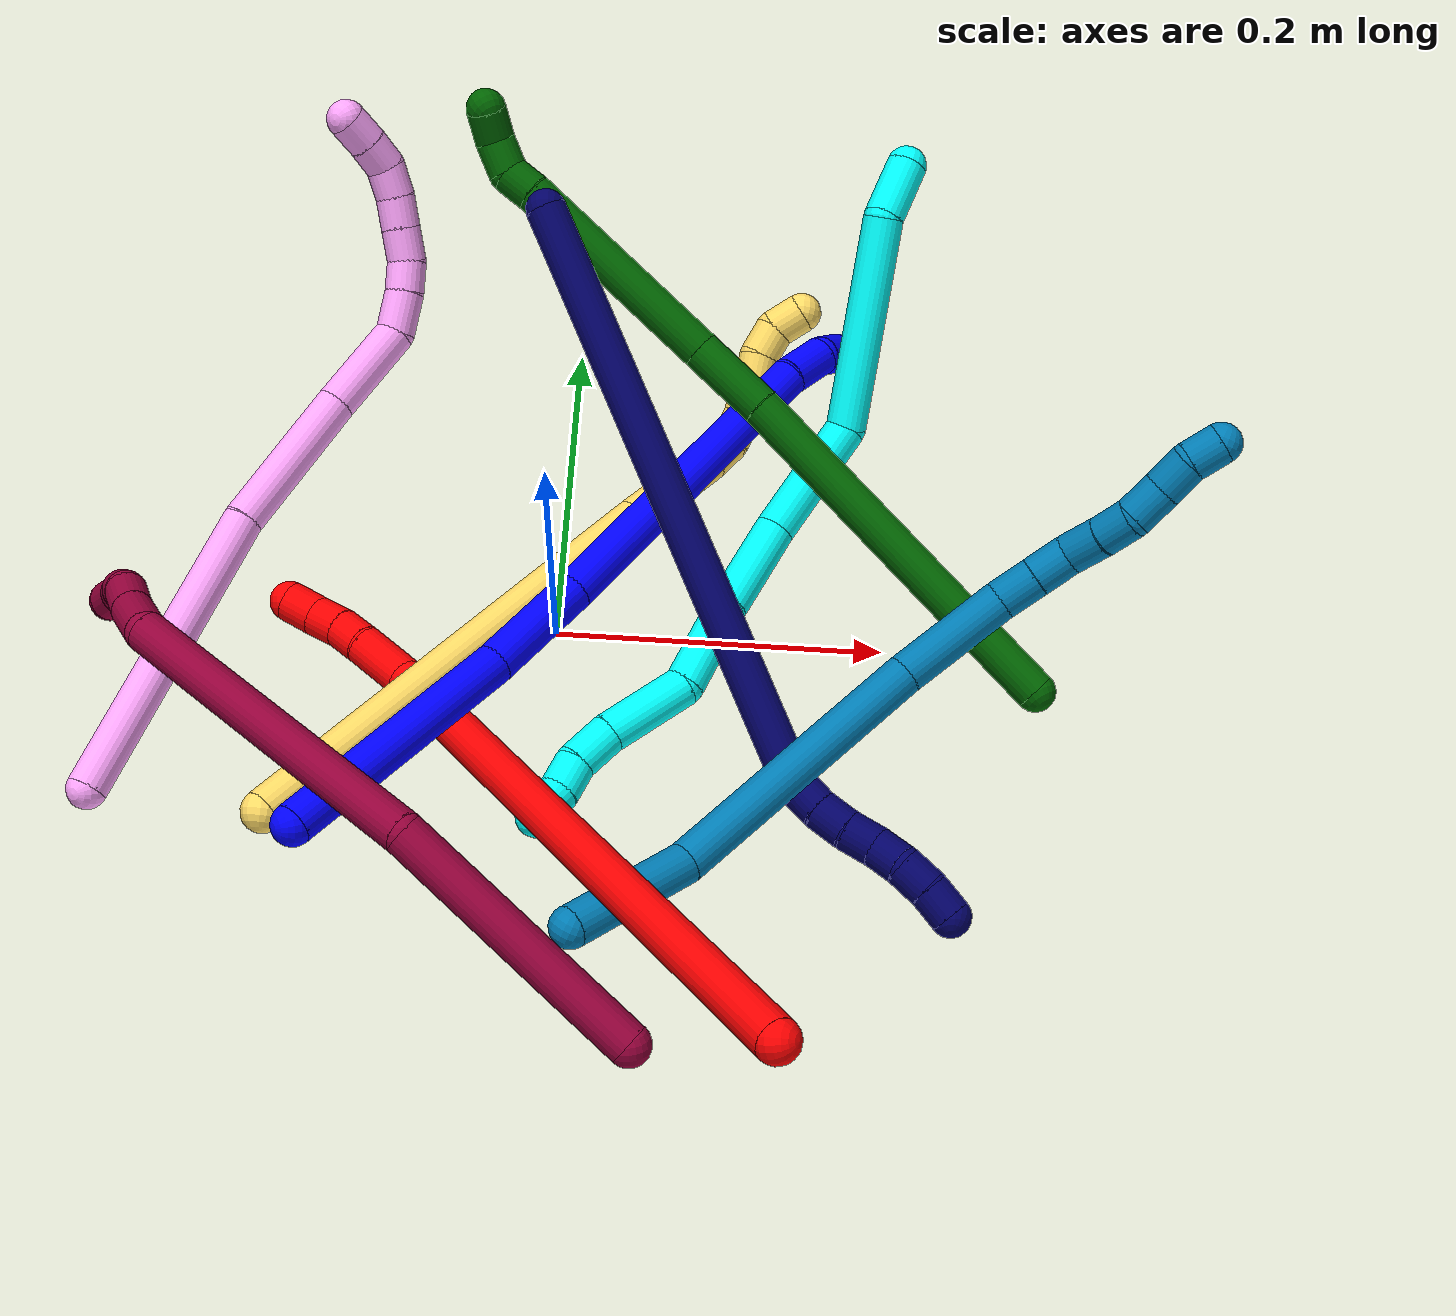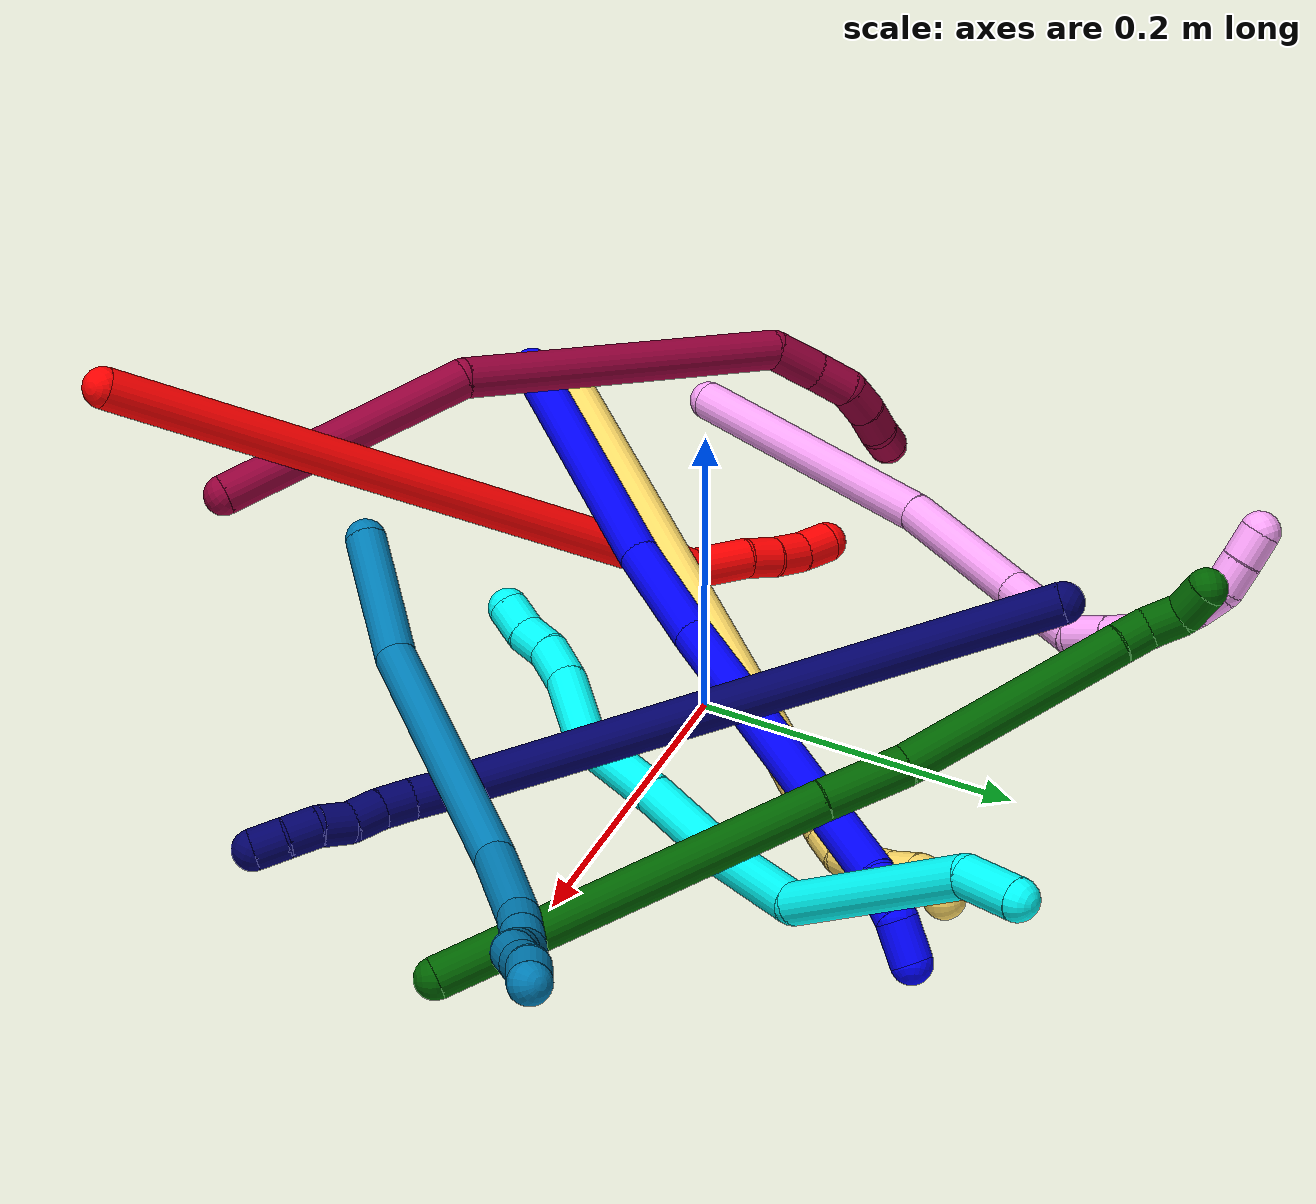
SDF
<sdf version="1.7">
 <world name="default">
  <plugin name="TubeGeneratorPlugin" filename="libtube_generator_plugin.so"/>
  <model name="photoneo_s_sensor">
   <static>1</static>
   <pose>0 0 2 1.57079 1.57079 3.14159</pose>
   <link name="link">
    <inertial><mass>0.1</mass></inertial>
    <sensor name="sensor" type="depth">
     <update_rate>30</update_rate>
     <camera>
      <horizontal_fov>1.22</horizontal_fov>
      <image><width>1920</width><height>1200</height><format>B8G8R8</format></image>
      <clip><near>0.1</near><far>4</far></clip>
      <depth_camera><output>points</output></depth_camera>
     </camera>
     <plugin name="camera_plugin" filename="libgazebo_ros_depth_camera.so">
      <baseline>0.2</baseline>
      <alwaysOn>1</alwaysOn>
      <updateRate>0.0</updateRate>
      <cameraName>camera_ir</cameraName>
      <imageTopicName>/camera/color/image_raw</imageTopicName>
      <cameraInfoTopicName>/camera/color/camera_info</cameraInfoTopicName>
      <depthImageTopicName>/camera/depth/image_raw</depthImageTopicName>
      <depthImageCameraInfoTopicName>/camera/depth/camera_info</depthImageCameraInfoTopicName>
      <pointCloudTopicName>/camera/depth/points</pointCloudTopicName>
      <frameName>fr_optical</frameName>
      <pointCloudCutoff>0.1</pointCloudCutoff>
      <pointCloudCutoffMax>2.0</pointCloudCutoffMax>
      <distortionK1>0</distortionK1>
      <distortionK2>0</distortionK2>
      <distortionK3>0</distortionK3>
      <distortionT1>0</distortionT1>
      <distortionT2>0</distortionT2>
      <CxPrime>0</CxPrime>
      <Cx>0</Cx>
      <Cy>0</Cy>
      <focalLength>0</focalLength>
      <hackBaseline>0</hackBaseline>
     </plugin>
    </sensor>
   </link>
  </model>
  <gravity>0 0 -9.8</gravity>
  <magnetic_field>6e-06 2.3e-05 -4.2e-05</magnetic_field>
  <atmosphere type="adiabatic"/>
  <physics name="default_physics" default="0" type="ode">
   <max_step_size>0.003</max_step_size>
   <real_time_factor>1</real_time_factor>
   <real_time_update_rate>1000</real_time_update_rate>
   <max_contacts>10000</max_contacts>
   <ode>
    <solver>
     <type>quick</type>
     <iters>100</iters>
     <sor>1.3</sor>
     <use_dynamic_moi_rescaling>0</use_dynamic_moi_rescaling>
    </solver>
    <constraints>
     <contact_max_correcting_vel>0</contact_max_correcting_vel>
     <contact_surface_layer>0.001</contact_surface_layer>
     <cfm>0</cfm>
     <erp>0.2</erp>
    </constraints>
   </ode>
  </physics>
  <scene><ambient>0.4 0.4 0.4 1</ambient><background>0.7 0.7 0.7 1</background><shadows>0</shadows></scene>
  <audio><device>default</device></audio>
  <spherical_coordinates>
   <surface_model>EARTH_WGS84</surface_model>
   <latitude_deg>0</latitude_deg>
   <longitude_deg>0</longitude_deg>
   <elevation>0</elevation>
   <heading_deg>0</heading_deg>
  </spherical_coordinates>
  <model name="bin">
   <static>1</static>
   <link name="bottom">
    <collision name="collision-bottom">
     <pose>0 0 -0.01 0 -0 0</pose>
     <geometry><box><size>0.8 0.6 0.02</size></box></geometry>
     <surface>
      <friction><ode><mu>100</mu><mu2>100</mu2></ode></friction>
      <contact><collide_bitmask>65535</collide_bitmask></contact>
     </surface>
    </collision>
   </link>
   <link name="west_wall">
    <collision name="collision-west_wall">
     <pose>-0.41 0 0.1 0 -0 0</pose>
     <geometry><box><size>0.02 0.6 0.2</size></box></geometry>
     <surface>
      <friction><ode><mu>100</mu><mu2>100</mu2></ode></friction>
      <contact><collide_bitmask>65535</collide_bitmask></contact>
     </surface>
    </collision>
   </link>
   <link name="east_wall">
    <collision name="collision-east_wall">
     <pose>0.41 0 0.1 0 -0 0</pose>
     <geometry><box><size>0.02 0.6 0.2</size></box></geometry>
     <surface>
      <friction><ode><mu>100</mu><mu2>100</mu2></ode></friction>
      <contact><collide_bitmask>65535</collide_bitmask></contact>
     </surface>
    </collision>
   </link>
   <link name="south_wall">
    <collision name="collision-south_wall">
     <pose>0 -0.31 0.1 0 -0 0</pose>
     <geometry><box><size>0.8 0.02 0.2</size></box></geometry>
     <surface>
      <friction><ode><mu>100</mu><mu2>100</mu2></ode></friction>
      <contact><collide_bitmask>65535</collide_bitmask></contact>
     </surface>
    </collision>
   </link>
   <link name="north_wall">
    <collision name="collision-north_wall">
     <pose>0 0.31 0.1 0 -0 0</pose>
     <geometry><box><size>0.8 0.02 0.2</size></box></geometry>
     <surface>
      <friction><ode><mu>100</mu><mu2>100</mu2></ode></friction>
      <contact><collide_bitmask>65535</collide_bitmask></contact>
     </surface>
    </collision>
   </link>
  </model>
  <model name="1">
   <static>0</static>
   <link name="1">
    <collision name="collision-cylinder-e_1_1_4">
     <pose>0.021194 0.023972 -0.073401 -2.82592 0.267883 -1.40506</pose>
     <geometry><cylinder><radius>0.0125</radius><length>0.160145</length></cylinder></geometry>
     <surface>
      <friction><ode><mu>1.16</mu><mu2>1.16</mu2><slip1>0</slip1><slip2>0</slip2></ode></friction>
      <contact><ode><kp>1e+06</kp><kd>1</kd><max_vel>0</max_vel><min_depth>0.001</min_depth></ode></contact>
     </surface>
    </collision>
    <visual name="visual-cylinder-e_1_1_4">
     <pose>0.021194 0.023972 -0.073401 -2.82592 0.267883 -1.40506</pose>
     <geometry><cylinder><radius>0.0125</radius><length>0.160145</length></cylinder></geometry>
     <material><ambient>0 0 1 1</ambient></material>
    </visual>
    <collision name="collision-cylinder-e_2_4_5">
     <pose>0.054491 0.059007 -0.177993 -2.80077 0.350574 -1.59956</pose>
     <geometry><cylinder><radius>0.0125</radius><length>0.070477</length></cylinder></geometry>
     <surface>
      <friction><ode><mu>1.16</mu><mu2>1.16</mu2><slip1>0</slip1><slip2>0</slip2></ode></friction>
      <contact><ode><kp>1e+06</kp><kd>1</kd><max_vel>0</max_vel><min_depth>0.001</min_depth></ode></contact>
     </surface>
    </collision>
    <visual name="visual-cylinder-e_2_4_5">
     <pose>0.054491 0.059007 -0.177993 -2.80077 0.350574 -1.59956</pose>
     <geometry><cylinder><radius>0.0125</radius><length>0.070477</length></cylinder></geometry>
     <material><ambient>0 0 1 1</ambient></material>
    </visual>
    <collision name="collision-cylinder-e_3_5_6">
     <pose>0.108871 0.102864 -0.301067 -2.79877 0.40893 -1.75035</pose>
     <geometry><cylinder><radius>0.0125</radius><length>0.212652</length></cylinder></geometry>
     <surface>
      <friction><ode><mu>1.16</mu><mu2>1.16</mu2><slip1>0</slip1><slip2>0</slip2></ode></friction>
      <contact><ode><kp>1e+06</kp><kd>1</kd><max_vel>0</max_vel><min_depth>0.001</min_depth></ode></contact>
     </surface>
    </collision>
    <visual name="visual-cylinder-e_3_5_6">
     <pose>0.108871 0.102864 -0.301067 -2.79877 0.40893 -1.75035</pose>
     <geometry><cylinder><radius>0.0125</radius><length>0.212652</length></cylinder></geometry>
     <material><ambient>0 0 1 1</ambient></material>
    </visual>
    <collision name="collision-cylinder-e_4_6_7">
     <pose>0.154483 0.139833 -0.407578 -2.86359 0.2157 -1.31724</pose>
     <geometry><cylinder><radius>0.0125</radius><length>0.031149</length></cylinder></geometry>
     <surface>
      <friction><ode><mu>1.16</mu><mu2>1.16</mu2><slip1>0</slip1><slip2>0</slip2></ode></friction>
      <contact><ode><kp>1e+06</kp><kd>1</kd><max_vel>0</max_vel><min_depth>0.001</min_depth></ode></contact>
     </surface>
    </collision>
    <visual name="visual-cylinder-e_4_6_7">
     <pose>0.154483 0.139833 -0.407578 -2.86359 0.2157 -1.31724</pose>
     <geometry><cylinder><radius>0.0125</radius><length>0.031149</length></cylinder></geometry>
     <material><ambient>0 0 1 1</ambient></material>
    </visual>
    <collision name="collision-cylinder-e_5_7_2">
     <pose>0.154474 0.149388 -0.433318 -2.69073 -0.264354 1.05077</pose>
     <geometry><cylinder><radius>0.0125</radius><length>0.025578</length></cylinder></geometry>
     <surface>
      <friction><ode><mu>1.16</mu><mu2>1.16</mu2><slip1>0</slip1><slip2>0</slip2></ode></friction>
      <contact><ode><kp>1e+06</kp><kd>1</kd><max_vel>0</max_vel><min_depth>0.001</min_depth></ode></contact>
     </surface>
    </collision>
    <visual name="visual-cylinder-e_5_7_2">
     <pose>0.154474 0.149388 -0.433318 -2.69073 -0.264354 1.05077</pose>
     <geometry><cylinder><radius>0.0125</radius><length>0.025578</length></cylinder></geometry>
     <material><ambient>0 0 1 1</ambient></material>
    </visual>
    <collision name="collision-sphere-2">
     <pose>0.151133 0.154767 -0.44443 0 -0 0</pose>
     <geometry><sphere><radius>0.0125</radius></sphere></geometry>
     <surface>
      <friction><ode><mu>1.16</mu><mu2>1.16</mu2><slip1>0</slip1><slip2>0</slip2></ode></friction>
      <contact><ode><kp>1e+06</kp><kd>1</kd><max_vel>0</max_vel><min_depth>0.001</min_depth></ode></contact>
     </surface>
    </collision>
    <visual name="visual-sphere-2">
     <pose>0.151133 0.154767 -0.44443 0 -0 0</pose>
     <geometry><sphere><radius>0.0125</radius></sphere></geometry>
     <material><ambient>0 0 1 1</ambient></material>
    </visual>
    <collision name="collision-sphere-7">
     <pose>0.157816 0.144008 -0.422207 0 -0 0</pose>
     <geometry><sphere><radius>0.0125</radius></sphere></geometry>
     <surface>
      <friction><ode><mu>1.16</mu><mu2>1.16</mu2><slip1>0</slip1><slip2>0</slip2></ode></friction>
      <contact><ode><kp>1e+06</kp><kd>1</kd><max_vel>0</max_vel><min_depth>0.001</min_depth></ode></contact>
     </surface>
    </collision>
    <visual name="visual-sphere-7">
     <pose>0.157816 0.144008 -0.422207 0 -0 0</pose>
     <geometry><sphere><radius>0.0125</radius></sphere></geometry>
     <material><ambient>0 0 1 1</ambient></material>
    </visual>
    <collision name="collision-sphere-6">
     <pose>0.151149 0.135658 -0.392948 0 -0 0</pose>
     <geometry><sphere><radius>0.0125</radius></sphere></geometry>
     <surface>
      <friction><ode><mu>1.16</mu><mu2>1.16</mu2><slip1>0</slip1><slip2>0</slip2></ode></friction>
      <contact><ode><kp>1e+06</kp><kd>1</kd><max_vel>0</max_vel><min_depth>0.001</min_depth></ode></contact>
     </surface>
    </collision>
    <visual name="visual-sphere-6">
     <pose>0.151149 0.135658 -0.392948 0 -0 0</pose>
     <geometry><sphere><radius>0.0125</radius></sphere></geometry>
     <material><ambient>0 0 1 1</ambient></material>
    </visual>
    <collision name="collision-sphere-5">
     <pose>0.066593 0.070069 -0.209185 0 -0 0</pose>
     <geometry><sphere><radius>0.0125</radius></sphere></geometry>
     <surface>
      <friction><ode><mu>1.16</mu><mu2>1.16</mu2><slip1>0</slip1><slip2>0</slip2></ode></friction>
      <contact><ode><kp>1e+06</kp><kd>1</kd><max_vel>0</max_vel><min_depth>0.001</min_depth></ode></contact>
     </surface>
    </collision>
    <visual name="visual-sphere-5">
     <pose>0.066593 0.070069 -0.209185 0 -0 0</pose>
     <geometry><sphere><radius>0.0125</radius></sphere></geometry>
     <material><ambient>0 0 1 1</ambient></material>
    </visual>
    <collision name="collision-sphere-1">
     <geometry><sphere><radius>0.0125</radius></sphere></geometry>
     <surface>
      <friction><ode><mu>1.16</mu><mu2>1.16</mu2><slip1>0</slip1><slip2>0</slip2></ode></friction>
      <contact><ode><kp>1e+06</kp><kd>1</kd><max_vel>0</max_vel><min_depth>0.001</min_depth></ode></contact>
     </surface>
    </collision>
    <visual name="visual-sphere-1">
     <geometry><sphere><radius>0.0125</radius></sphere></geometry>
     <material><ambient>0 0 1 1</ambient></material>
    </visual>
    <collision name="collision-sphere-4">
     <pose>0.042389 0.047944 -0.146802 0 -0 0</pose>
     <geometry><sphere><radius>0.0125</radius></sphere></geometry>
     <surface>
      <friction><ode><mu>1.16</mu><mu2>1.16</mu2><slip1>0</slip1><slip2>0</slip2></ode></friction>
      <contact><ode><kp>1e+06</kp><kd>1</kd><max_vel>0</max_vel><min_depth>0.001</min_depth></ode></contact>
     </surface>
    </collision>
    <visual name="visual-sphere-4">
     <pose>0.042389 0.047944 -0.146802 0 -0 0</pose>
     <geometry><sphere><radius>0.0125</radius></sphere></geometry>
     <material><ambient>0 0 1 1</ambient></material>
    </visual>
    <inertial>
     <pose>0.078299 0.076097 -0.224201 0 -0 0</pose>
     <mass>0.5</mass>
     <inertia>
      <ixx>-0.001158</ixx>
      <ixy>0</ixy>
      <ixz>0</ixz>
      <iyy>-0.000863</iyy>
      <iyz>0</iyz>
      <izz>-0.000826</izz>
     </inertia>
    </inertial>
   </link>
   <pose>-0.125415 -0.179439 0.112991 -0.716134 -1.01635 1.29852</pose>
  </model>
  <model name="2">
   <static>0</static>
   <link name="2">
    <collision name="collision-cylinder-e_1_1_4">
     <pose>-0.054766 0.105555 -0.161891 -2.5638 -0.276135 0.874656</pose>
     <geometry><cylinder><radius>0.0125</radius><length>0.401745</length></cylinder></geometry>
     <surface>
      <friction><ode><mu>1.16</mu><mu2>1.16</mu2><slip1>0</slip1><slip2>0</slip2></ode></friction>
      <contact><ode><kp>1e+06</kp><kd>1</kd><max_vel>0</max_vel><min_depth>0.001</min_depth></ode></contact>
     </surface>
    </collision>
    <visual name="visual-cylinder-e_1_1_4">
     <pose>-0.054766 0.105555 -0.161891 -2.5638 -0.276135 0.874656</pose>
     <geometry><cylinder><radius>0.0125</radius><length>0.401745</length></cylinder></geometry>
     <material><ambient>1 0 0 1</ambient></material>
    </visual>
    <collision name="collision-cylinder-e_2_4_5">
     <pose>-0.119927 0.214545 -0.338696 -2.91524 -0.596665 2.43349</pose>
     <geometry><cylinder><radius>0.0125</radius><length>0.037003</length></cylinder></geometry>
     <surface>
      <friction><ode><mu>1.16</mu><mu2>1.16</mu2><slip1>0</slip1><slip2>0</slip2></ode></friction>
      <contact><ode><kp>1e+06</kp><kd>1</kd><max_vel>0</max_vel><min_depth>0.001</min_depth></ode></contact>
     </surface>
    </collision>
    <visual name="visual-cylinder-e_2_4_5">
     <pose>-0.119927 0.214545 -0.338696 -2.91524 -0.596665 2.43349</pose>
     <geometry><cylinder><radius>0.0125</radius><length>0.037003</length></cylinder></geometry>
     <material><ambient>1 0 0 1</ambient></material>
    </visual>
    <collision name="collision-cylinder-e_3_5_6">
     <pose>-0.134783 0.220891 -0.362161 -2.81338 -0.458634 1.90754</pose>
     <geometry><cylinder><radius>0.0125</radius><length>0.020148</length></cylinder></geometry>
     <surface>
      <friction><ode><mu>1.16</mu><mu2>1.16</mu2><slip1>0</slip1><slip2>0</slip2></ode></friction>
      <contact><ode><kp>1e+06</kp><kd>1</kd><max_vel>0</max_vel><min_depth>0.001</min_depth></ode></contact>
     </surface>
    </collision>
    <visual name="visual-cylinder-e_3_5_6">
     <pose>-0.134783 0.220891 -0.362161 -2.81338 -0.458634 1.90754</pose>
     <geometry><cylinder><radius>0.0125</radius><length>0.020148</length></cylinder></geometry>
     <material><ambient>1 0 0 1</ambient></material>
    </visual>
    <collision name="collision-cylinder-e_4_6_7">
     <pose>-0.143308 0.22515 -0.379944 -2.9967 -0.410864 2.47131</pose>
     <geometry><cylinder><radius>0.0125</radius><length>0.020355</length></cylinder></geometry>
     <surface>
      <friction><ode><mu>1.16</mu><mu2>1.16</mu2><slip1>0</slip1><slip2>0</slip2></ode></friction>
      <contact><ode><kp>1e+06</kp><kd>1</kd><max_vel>0</max_vel><min_depth>0.001</min_depth></ode></contact>
     </surface>
    </collision>
    <visual name="visual-cylinder-e_4_6_7">
     <pose>-0.143308 0.22515 -0.379944 -2.9967 -0.410864 2.47131</pose>
     <geometry><cylinder><radius>0.0125</radius><length>0.020355</length></cylinder></geometry>
     <material><ambient>1 0 0 1</ambient></material>
    </visual>
    <collision name="collision-cylinder-e_5_7_2">
     <pose>-0.15271 0.226621 -0.398072 -3.1277 -0.540376 3.09143</pose>
     <geometry><cylinder><radius>0.0125</radius><length>0.02075</length></cylinder></geometry>
     <surface>
      <friction><ode><mu>1.16</mu><mu2>1.16</mu2><slip1>0</slip1><slip2>0</slip2></ode></friction>
      <contact><ode><kp>1e+06</kp><kd>1</kd><max_vel>0</max_vel><min_depth>0.001</min_depth></ode></contact>
     </surface>
    </collision>
    <visual name="visual-cylinder-e_5_7_2">
     <pose>-0.15271 0.226621 -0.398072 -3.1277 -0.540376 3.09143</pose>
     <geometry><cylinder><radius>0.0125</radius><length>0.02075</length></cylinder></geometry>
     <material><ambient>1 0 0 1</ambient></material>
    </visual>
    <collision name="collision-sphere-2">
     <pose>-0.158047 0.226745 -0.406968 0 -0 0</pose>
     <geometry><sphere><radius>0.0125</radius></sphere></geometry>
     <surface>
      <friction><ode><mu>1.16</mu><mu2>1.16</mu2><slip1>0</slip1><slip2>0</slip2></ode></friction>
      <contact><ode><kp>1e+06</kp><kd>1</kd><max_vel>0</max_vel><min_depth>0.001</min_depth></ode></contact>
     </surface>
    </collision>
    <visual name="visual-sphere-2">
     <pose>-0.158047 0.226745 -0.406968 0 -0 0</pose>
     <geometry><sphere><radius>0.0125</radius></sphere></geometry>
     <material><ambient>1 0 0 1</ambient></material>
    </visual>
    <collision name="collision-sphere-7">
     <pose>-0.147372 0.226497 -0.389176 0 -0 0</pose>
     <geometry><sphere><radius>0.0125</radius></sphere></geometry>
     <surface>
      <friction><ode><mu>1.16</mu><mu2>1.16</mu2><slip1>0</slip1><slip2>0</slip2></ode></friction>
      <contact><ode><kp>1e+06</kp><kd>1</kd><max_vel>0</max_vel><min_depth>0.001</min_depth></ode></contact>
     </surface>
    </collision>
    <visual name="visual-sphere-7">
     <pose>-0.147372 0.226497 -0.389176 0 -0 0</pose>
     <geometry><sphere><radius>0.0125</radius></sphere></geometry>
     <material><ambient>1 0 0 1</ambient></material>
    </visual>
    <collision name="collision-sphere-6">
     <pose>-0.139243 0.223803 -0.370711 0 -0 0</pose>
     <geometry><sphere><radius>0.0125</radius></sphere></geometry>
     <surface>
      <friction><ode><mu>1.16</mu><mu2>1.16</mu2><slip1>0</slip1><slip2>0</slip2></ode></friction>
      <contact><ode><kp>1e+06</kp><kd>1</kd><max_vel>0</max_vel><min_depth>0.001</min_depth></ode></contact>
     </surface>
    </collision>
    <visual name="visual-sphere-6">
     <pose>-0.139243 0.223803 -0.370711 0 -0 0</pose>
     <geometry><sphere><radius>0.0125</radius></sphere></geometry>
     <material><ambient>1 0 0 1</ambient></material>
    </visual>
    <collision name="collision-sphere-5">
     <pose>-0.130323 0.21798 -0.35361 0 -0 0</pose>
     <geometry><sphere><radius>0.0125</radius></sphere></geometry>
     <surface>
      <friction><ode><mu>1.16</mu><mu2>1.16</mu2><slip1>0</slip1><slip2>0</slip2></ode></friction>
      <contact><ode><kp>1e+06</kp><kd>1</kd><max_vel>0</max_vel><min_depth>0.001</min_depth></ode></contact>
     </surface>
    </collision>
    <visual name="visual-sphere-5">
     <pose>-0.130323 0.21798 -0.35361 0 -0 0</pose>
     <geometry><sphere><radius>0.0125</radius></sphere></geometry>
     <material><ambient>1 0 0 1</ambient></material>
    </visual>
    <collision name="collision-sphere-1">
     <geometry><sphere><radius>0.0125</radius></sphere></geometry>
     <surface>
      <friction><ode><mu>1.16</mu><mu2>1.16</mu2><slip1>0</slip1><slip2>0</slip2></ode></friction>
      <contact><ode><kp>1e+06</kp><kd>1</kd><max_vel>0</max_vel><min_depth>0.001</min_depth></ode></contact>
     </surface>
    </collision>
    <visual name="visual-sphere-1">
     <geometry><sphere><radius>0.0125</radius></sphere></geometry>
     <material><ambient>1 0 0 1</ambient></material>
    </visual>
    <collision name="collision-sphere-4">
     <pose>-0.109531 0.21111 -0.323781 0 -0 0</pose>
     <geometry><sphere><radius>0.0125</radius></sphere></geometry>
     <surface>
      <friction><ode><mu>1.16</mu><mu2>1.16</mu2><slip1>0</slip1><slip2>0</slip2></ode></friction>
      <contact><ode><kp>1e+06</kp><kd>1</kd><max_vel>0</max_vel><min_depth>0.001</min_depth></ode></contact>
     </surface>
    </collision>
    <visual name="visual-sphere-4">
     <pose>-0.109531 0.21111 -0.323781 0 -0 0</pose>
     <geometry><sphere><radius>0.0125</radius></sphere></geometry>
     <material><ambient>1 0 0 1</ambient></material>
    </visual>
    <inertial>
     <pose>-0.070481 0.128161 -0.201723 0 -0 0</pose>
     <mass>0.5</mass>
     <inertia>
      <ixx>0.007331</ixx>
      <ixy>0</ixy>
      <ixz>0</ixz>
      <iyy>0.00174</iyy>
      <iyz>0</iyz>
      <izz>-0.001398</izz>
     </inertia>
    </inertial>
   </link>
   <pose>0.13931 -0.316263 0.226499 -0.866556 0.741483 -1.19155</pose>
  </model>
  <model name="3">
   <static>0</static>
   <link name="3">
    <collision name="collision-cylinder-e_1_1_4">
     <pose>-0.001632 -0.00032 -0.018961 3.12474 -0.085861 -2.75425</pose>
     <geometry><cylinder><radius>0.0125</radius><length>0.038068</length></cylinder></geometry>
     <surface>
      <friction><ode><mu>1.16</mu><mu2>1.16</mu2><slip1>0</slip1><slip2>0</slip2></ode></friction>
      <contact><ode><kp>1e+06</kp><kd>1</kd><max_vel>0</max_vel><min_depth>0.001</min_depth></ode></contact>
     </surface>
    </collision>
    <visual name="visual-cylinder-e_1_1_4">
     <pose>-0.001632 -0.00032 -0.018961 3.12474 -0.085861 -2.75425</pose>
     <geometry><cylinder><radius>0.0125</radius><length>0.038068</length></cylinder></geometry>
     <material><ambient>0.003922 1 0.996078 1</ambient></material>
    </visual>
    <collision name="collision-cylinder-e_2_4_5">
     <pose>-0.004627 0.027101 -0.09818 -2.71016 -0.020532 0.093633</pose>
     <geometry><cylinder><radius>0.0125</radius><length>0.1327</length></cylinder></geometry>
     <surface>
      <friction><ode><mu>1.16</mu><mu2>1.16</mu2><slip1>0</slip1><slip2>0</slip2></ode></friction>
      <contact><ode><kp>1e+06</kp><kd>1</kd><max_vel>0</max_vel><min_depth>0.001</min_depth></ode></contact>
     </surface>
    </collision>
    <visual name="visual-cylinder-e_2_4_5">
     <pose>-0.004627 0.027101 -0.09818 -2.71016 -0.020532 0.093633</pose>
     <geometry><cylinder><radius>0.0125</radius><length>0.1327</length></cylinder></geometry>
     <material><ambient>0.003922 1 0.996078 1</ambient></material>
    </visual>
    <collision name="collision-cylinder-e_3_5_6">
     <pose>-0.018281 0.055393 -0.195499 -3.12672 -0.320217 3.04957</pose>
     <geometry><cylinder><radius>0.0125</radius><length>0.078102</length></cylinder></geometry>
     <surface>
      <friction><ode><mu>1.16</mu><mu2>1.16</mu2><slip1>0</slip1><slip2>0</slip2></ode></friction>
      <contact><ode><kp>1e+06</kp><kd>1</kd><max_vel>0</max_vel><min_depth>0.001</min_depth></ode></contact>
     </surface>
    </collision>
    <visual name="visual-cylinder-e_3_5_6">
     <pose>-0.018281 0.055393 -0.195499 -3.12672 -0.320217 3.04957</pose>
     <geometry><cylinder><radius>0.0125</radius><length>0.078102</length></cylinder></geometry>
     <material><ambient>0.003922 1 0.996078 1</ambient></material>
    </visual>
    <collision name="collision-cylinder-e_4_6_7">
     <pose>-0.033223 0.046602 -0.262773 2.84171 -0.083593 -0.540118</pose>
     <geometry><cylinder><radius>0.0125</radius><length>0.063468</length></cylinder></geometry>
     <surface>
      <friction><ode><mu>1.16</mu><mu2>1.16</mu2><slip1>0</slip1><slip2>0</slip2></ode></friction>
      <contact><ode><kp>1e+06</kp><kd>1</kd><max_vel>0</max_vel><min_depth>0.001</min_depth></ode></contact>
     </surface>
    </collision>
    <visual name="visual-cylinder-e_4_6_7">
     <pose>-0.033223 0.046602 -0.262773 2.84171 -0.083593 -0.540118</pose>
     <geometry><cylinder><radius>0.0125</radius><length>0.063468</length></cylinder></geometry>
     <material><ambient>0.003922 1 0.996078 1</ambient></material>
    </visual>
    <collision name="collision-cylinder-e_5_7_8">
     <pose>-0.037548 0.029724 -0.322526 2.89181 -0.054902 -0.430639</pose>
     <geometry><cylinder><radius>0.0125</radius><length>0.061068</length></cylinder></geometry>
     <surface>
      <friction><ode><mu>1.16</mu><mu2>1.16</mu2><slip1>0</slip1><slip2>0</slip2></ode></friction>
      <contact><ode><kp>1e+06</kp><kd>1</kd><max_vel>0</max_vel><min_depth>0.001</min_depth></ode></contact>
     </surface>
    </collision>
    <visual name="visual-cylinder-e_5_7_8">
     <pose>-0.037548 0.029724 -0.322526 2.89181 -0.054902 -0.430639</pose>
     <geometry><cylinder><radius>0.0125</radius><length>0.061068</length></cylinder></geometry>
     <material><ambient>0.003922 1 0.996078 1</ambient></material>
    </visual>
    <collision name="collision-cylinder-e_6_8_9">
     <pose>-0.05307 0.012532 -0.374024 2.72731 -0.523534 -1.81125</pose>
     <geometry><cylinder><radius>0.0125</radius><length>0.055391</length></cylinder></geometry>
     <surface>
      <friction><ode><mu>1.16</mu><mu2>1.16</mu2><slip1>0</slip1><slip2>0</slip2></ode></friction>
      <contact><ode><kp>1e+06</kp><kd>1</kd><max_vel>0</max_vel><min_depth>0.001</min_depth></ode></contact>
     </surface>
    </collision>
    <visual name="visual-cylinder-e_6_8_9">
     <pose>-0.05307 0.012532 -0.374024 2.72731 -0.523534 -1.81125</pose>
     <geometry><cylinder><radius>0.0125</radius><length>0.055391</length></cylinder></geometry>
     <material><ambient>0.003922 1 0.996078 1</ambient></material>
    </visual>
    <collision name="collision-cylinder-e_7_9_10">
     <pose>-0.071288 -0.002454 -0.408143 2.72849 -0.318072 -1.30661</pose>
     <geometry><cylinder><radius>0.0125</radius><length>0.027961</length></cylinder></geometry>
     <surface>
      <friction><ode><mu>1.16</mu><mu2>1.16</mu2><slip1>0</slip1><slip2>0</slip2></ode></friction>
      <contact><ode><kp>1e+06</kp><kd>1</kd><max_vel>0</max_vel><min_depth>0.001</min_depth></ode></contact>
     </surface>
    </collision>
    <visual name="visual-cylinder-e_7_9_10">
     <pose>-0.071288 -0.002454 -0.408143 2.72849 -0.318072 -1.30661</pose>
     <geometry><cylinder><radius>0.0125</radius><length>0.027961</length></cylinder></geometry>
     <material><ambient>0.003922 1 0.996078 1</ambient></material>
    </visual>
    <collision name="collision-cylinder-e_8_10_11">
     <pose>-0.076396 -0.010418 -0.430685 2.89319 -0.068566 -0.536193</pose>
     <geometry><cylinder><radius>0.0125</radius><length>0.021467</length></cylinder></geometry>
     <surface>
      <friction><ode><mu>1.16</mu><mu2>1.16</mu2><slip1>0</slip1><slip2>0</slip2></ode></friction>
      <contact><ode><kp>1e+06</kp><kd>1</kd><max_vel>0</max_vel><min_depth>0.001</min_depth></ode></contact>
     </surface>
    </collision>
    <visual name="visual-cylinder-e_8_10_11">
     <pose>-0.076396 -0.010418 -0.430685 2.89319 -0.068566 -0.536193</pose>
     <geometry><cylinder><radius>0.0125</radius><length>0.021467</length></cylinder></geometry>
     <material><ambient>0.003922 1 0.996078 1</ambient></material>
    </visual>
    <collision name="collision-cylinder-e_9_11_2">
     <pose>-0.078774 -0.018266 -0.45048 2.6357 -0.151452 -0.571009</pose>
     <geometry><cylinder><radius>0.0125</radius><length>0.021776</length></cylinder></geometry>
     <surface>
      <friction><ode><mu>1.16</mu><mu2>1.16</mu2><slip1>0</slip1><slip2>0</slip2></ode></friction>
      <contact><ode><kp>1e+06</kp><kd>1</kd><max_vel>0</max_vel><min_depth>0.001</min_depth></ode></contact>
     </surface>
    </collision>
    <visual name="visual-cylinder-e_9_11_2">
     <pose>-0.078774 -0.018266 -0.45048 2.6357 -0.151452 -0.571009</pose>
     <geometry><cylinder><radius>0.0125</radius><length>0.021776</length></cylinder></geometry>
     <material><ambient>0.003922 1 0.996078 1</ambient></material>
    </visual>
    <collision name="collision-sphere-2">
     <pose>-0.080417 -0.023482 -0.459895 0 -0 0</pose>
     <geometry><sphere><radius>0.0125</radius></sphere></geometry>
     <surface>
      <friction><ode><mu>1.16</mu><mu2>1.16</mu2><slip1>0</slip1><slip2>0</slip2></ode></friction>
      <contact><ode><kp>1e+06</kp><kd>1</kd><max_vel>0</max_vel><min_depth>0.001</min_depth></ode></contact>
     </surface>
    </collision>
    <visual name="visual-sphere-2">
     <pose>-0.080417 -0.023482 -0.459895 0 -0 0</pose>
     <geometry><sphere><radius>0.0125</radius></sphere></geometry>
     <material><ambient>0.003922 1 0.996078 1</ambient></material>
    </visual>
    <collision name="collision-sphere-11">
     <pose>-0.077131 -0.01305 -0.441065 0 -0 0</pose>
     <geometry><sphere><radius>0.0125</radius></sphere></geometry>
     <surface>
      <friction><ode><mu>1.16</mu><mu2>1.16</mu2><slip1>0</slip1><slip2>0</slip2></ode></friction>
      <contact><ode><kp>1e+06</kp><kd>1</kd><max_vel>0</max_vel><min_depth>0.001</min_depth></ode></contact>
     </surface>
    </collision>
    <visual name="visual-sphere-11">
     <pose>-0.077131 -0.01305 -0.441065 0 -0 0</pose>
     <geometry><sphere><radius>0.0125</radius></sphere></geometry>
     <material><ambient>0.003922 1 0.996078 1</ambient></material>
    </visual>
    <collision name="collision-sphere-10">
     <pose>-0.07566 -0.007785 -0.420305 0 -0 0</pose>
     <geometry><sphere><radius>0.0125</radius></sphere></geometry>
     <surface>
      <friction><ode><mu>1.16</mu><mu2>1.16</mu2><slip1>0</slip1><slip2>0</slip2></ode></friction>
      <contact><ode><kp>1e+06</kp><kd>1</kd><max_vel>0</max_vel><min_depth>0.001</min_depth></ode></contact>
     </surface>
    </collision>
    <visual name="visual-sphere-10">
     <pose>-0.07566 -0.007785 -0.420305 0 -0 0</pose>
     <geometry><sphere><radius>0.0125</radius></sphere></geometry>
     <material><ambient>0.003922 1 0.996078 1</ambient></material>
    </visual>
    <collision name="collision-sphere-9">
     <pose>-0.066916 0.002877 -0.395981 0 -0 0</pose>
     <geometry><sphere><radius>0.0125</radius></sphere></geometry>
     <surface>
      <friction><ode><mu>1.16</mu><mu2>1.16</mu2><slip1>0</slip1><slip2>0</slip2></ode></friction>
      <contact><ode><kp>1e+06</kp><kd>1</kd><max_vel>0</max_vel><min_depth>0.001</min_depth></ode></contact>
     </surface>
    </collision>
    <visual name="visual-sphere-9">
     <pose>-0.066916 0.002877 -0.395981 0 -0 0</pose>
     <geometry><sphere><radius>0.0125</radius></sphere></geometry>
     <material><ambient>0.003922 1 0.996078 1</ambient></material>
    </visual>
    <collision name="collision-sphere-4">
     <pose>-0.003265 -0.000639 -0.037922 0 -0 0</pose>
     <geometry><sphere><radius>0.0125</radius></sphere></geometry>
     <surface>
      <friction><ode><mu>1.16</mu><mu2>1.16</mu2><slip1>0</slip1><slip2>0</slip2></ode></friction>
      <contact><ode><kp>1e+06</kp><kd>1</kd><max_vel>0</max_vel><min_depth>0.001</min_depth></ode></contact>
     </surface>
    </collision>
    <visual name="visual-sphere-4">
     <pose>-0.003265 -0.000639 -0.037922 0 -0 0</pose>
     <geometry><sphere><radius>0.0125</radius></sphere></geometry>
     <material><ambient>0.003922 1 0.996078 1</ambient></material>
    </visual>
    <collision name="collision-sphere-1">
     <geometry><sphere><radius>0.0125</radius></sphere></geometry>
     <surface>
      <friction><ode><mu>1.16</mu><mu2>1.16</mu2><slip1>0</slip1><slip2>0</slip2></ode></friction>
      <contact><ode><kp>1e+06</kp><kd>1</kd><max_vel>0</max_vel><min_depth>0.001</min_depth></ode></contact>
     </surface>
    </collision>
    <visual name="visual-sphere-1">
     <geometry><sphere><radius>0.0125</radius></sphere></geometry>
     <material><ambient>0.003922 1 0.996078 1</ambient></material>
    </visual>
    <collision name="collision-sphere-8">
     <pose>-0.039224 0.022187 -0.352068 0 -0 0</pose>
     <geometry><sphere><radius>0.0125</radius></sphere></geometry>
     <surface>
      <friction><ode><mu>1.16</mu><mu2>1.16</mu2><slip1>0</slip1><slip2>0</slip2></ode></friction>
      <contact><ode><kp>1e+06</kp><kd>1</kd><max_vel>0</max_vel><min_depth>0.001</min_depth></ode></contact>
     </surface>
    </collision>
    <visual name="visual-sphere-8">
     <pose>-0.039224 0.022187 -0.352068 0 -0 0</pose>
     <geometry><sphere><radius>0.0125</radius></sphere></geometry>
     <material><ambient>0.003922 1 0.996078 1</ambient></material>
    </visual>
    <collision name="collision-sphere-5">
     <pose>-0.005989 0.054841 -0.158437 0 -0 0</pose>
     <geometry><sphere><radius>0.0125</radius></sphere></geometry>
     <surface>
      <friction><ode><mu>1.16</mu><mu2>1.16</mu2><slip1>0</slip1><slip2>0</slip2></ode></friction>
      <contact><ode><kp>1e+06</kp><kd>1</kd><max_vel>0</max_vel><min_depth>0.001</min_depth></ode></contact>
     </surface>
    </collision>
    <visual name="visual-sphere-5">
     <pose>-0.005989 0.054841 -0.158437 0 -0 0</pose>
     <geometry><sphere><radius>0.0125</radius></sphere></geometry>
     <material><ambient>0.003922 1 0.996078 1</ambient></material>
    </visual>
    <collision name="collision-sphere-6">
     <pose>-0.030573 0.055944 -0.232561 0 -0 0</pose>
     <geometry><sphere><radius>0.0125</radius></sphere></geometry>
     <surface>
      <friction><ode><mu>1.16</mu><mu2>1.16</mu2><slip1>0</slip1><slip2>0</slip2></ode></friction>
      <contact><ode><kp>1e+06</kp><kd>1</kd><max_vel>0</max_vel><min_depth>0.001</min_depth></ode></contact>
     </surface>
    </collision>
    <visual name="visual-sphere-6">
     <pose>-0.030573 0.055944 -0.232561 0 -0 0</pose>
     <geometry><sphere><radius>0.0125</radius></sphere></geometry>
     <material><ambient>0.003922 1 0.996078 1</ambient></material>
    </visual>
    <collision name="collision-sphere-7">
     <pose>-0.035873 0.03726 -0.292984 0 -0 0</pose>
     <geometry><sphere><radius>0.0125</radius></sphere></geometry>
     <surface>
      <friction><ode><mu>1.16</mu><mu2>1.16</mu2><slip1>0</slip1><slip2>0</slip2></ode></friction>
      <contact><ode><kp>1e+06</kp><kd>1</kd><max_vel>0</max_vel><min_depth>0.001</min_depth></ode></contact>
     </surface>
    </collision>
    <visual name="visual-sphere-7">
     <pose>-0.035873 0.03726 -0.292984 0 -0 0</pose>
     <geometry><sphere><radius>0.0125</radius></sphere></geometry>
     <material><ambient>0.003922 1 0.996078 1</ambient></material>
    </visual>
    <inertial>
     <pose>-0.029587 0.025375 -0.233155 0 -0 0</pose>
     <mass>0.5</mass>
     <inertia>
      <ixx>0.000167</ixx>
      <ixy>0</ixy>
      <ixz>0</ixz>
      <iyy>-0.000187</iyy>
      <iyz>0</iyz>
      <izz>-6.9e-05</izz>
     </inertia>
    </inertial>
   </link>
   <pose>0.19887 0.281077 0.117123 -1.37277 -0.302711 -0.324055</pose>
  </model>
  <model name="4">
   <static>0</static>
   <link name="4">
    <collision name="collision-cylinder-e_1_1_4">
     <pose>0.010839 0.070117 0.064703 -0.825538 0.113125 -0.049583</pose>
     <geometry><cylinder><radius>0.0125</radius><length>0.192045</length></cylinder></geometry>
     <surface>
      <friction><ode><mu>1.16</mu><mu2>1.16</mu2><slip1>0</slip1><slip2>0</slip2></ode></friction>
      <contact><ode><kp>1e+06</kp><kd>1</kd><max_vel>0</max_vel><min_depth>0.001</min_depth></ode></contact>
     </surface>
    </collision>
    <visual name="visual-cylinder-e_1_1_4">
     <pose>0.010839 0.070117 0.064703 -0.825538 0.113125 -0.049583</pose>
     <geometry><cylinder><radius>0.0125</radius><length>0.192045</length></cylinder></geometry>
     <material><ambient>1 0.65098 0.996078 1</ambient></material>
    </visual>
    <collision name="collision-cylinder-e_2_4_5">
     <pose>0.021666 0.173522 0.165441 -0.745786 -0.000262 0.000103</pose>
     <geometry><cylinder><radius>0.0125</radius><length>0.098116</length></cylinder></geometry>
     <surface>
      <friction><ode><mu>1.16</mu><mu2>1.16</mu2><slip1>0</slip1><slip2>0</slip2></ode></friction>
      <contact><ode><kp>1e+06</kp><kd>1</kd><max_vel>0</max_vel><min_depth>0.001</min_depth></ode></contact>
     </surface>
    </collision>
    <visual name="visual-cylinder-e_2_4_5">
     <pose>0.021666 0.173522 0.165441 -0.745786 -0.000262 0.000103</pose>
     <geometry><cylinder><radius>0.0125</radius><length>0.098116</length></cylinder></geometry>
     <material><ambient>1 0.65098 0.996078 1</ambient></material>
    </visual>
    <collision name="collision-cylinder-e_3_5_6">
     <pose>0.019259 0.228958 0.222103 -0.820949 -0.078937 0.034367</pose>
     <geometry><cylinder><radius>0.0125</radius><length>0.060718</length></cylinder></geometry>
     <surface>
      <friction><ode><mu>1.16</mu><mu2>1.16</mu2><slip1>0</slip1><slip2>0</slip2></ode></friction>
      <contact><ode><kp>1e+06</kp><kd>1</kd><max_vel>0</max_vel><min_depth>0.001</min_depth></ode></contact>
     </surface>
    </collision>
    <visual name="visual-cylinder-e_3_5_6">
     <pose>0.019259 0.228958 0.222103 -0.820949 -0.078937 0.034367</pose>
     <geometry><cylinder><radius>0.0125</radius><length>0.060718</length></cylinder></geometry>
     <material><ambient>1 0.65098 0.996078 1</ambient></material>
    </visual>
    <collision name="collision-cylinder-e_4_6_7">
     <pose>0.020195 0.263242 0.247609 -1.18849 0.249219 -0.168878</pose>
     <geometry><cylinder><radius>0.0125</radius><length>0.026997</length></cylinder></geometry>
     <surface>
      <friction><ode><mu>1.16</mu><mu2>1.16</mu2><slip1>0</slip1><slip2>0</slip2></ode></friction>
      <contact><ode><kp>1e+06</kp><kd>1</kd><max_vel>0</max_vel><min_depth>0.001</min_depth></ode></contact>
     </surface>
    </collision>
    <visual name="visual-cylinder-e_4_6_7">
     <pose>0.020195 0.263242 0.247609 -1.18849 0.249219 -0.168878</pose>
     <geometry><cylinder><radius>0.0125</radius><length>0.026997</length></cylinder></geometry>
     <material><ambient>1 0.65098 0.996078 1</ambient></material>
    </visual>
    <collision name="collision-cylinder-e_5_7_8">
     <pose>0.027099 0.284314 0.25523 -1.27313 0.365373 -0.271455</pose>
     <geometry><cylinder><radius>0.0125</radius><length>0.020012</length></cylinder></geometry>
     <surface>
      <friction><ode><mu>1.16</mu><mu2>1.16</mu2><slip1>0</slip1><slip2>0</slip2></ode></friction>
      <contact><ode><kp>1e+06</kp><kd>1</kd><max_vel>0</max_vel><min_depth>0.001</min_depth></ode></contact>
     </surface>
    </collision>
    <visual name="visual-cylinder-e_5_7_8">
     <pose>0.027099 0.284314 0.25523 -1.27313 0.365373 -0.271455</pose>
     <geometry><cylinder><radius>0.0125</radius><length>0.020012</length></cylinder></geometry>
     <material><ambient>1 0.65098 0.996078 1</ambient></material>
    </visual>
    <collision name="collision-cylinder-e_6_8_9">
     <pose>0.035871 0.302774 0.257813 -1.58732 0.499366 -0.507338</pose>
     <geometry><cylinder><radius>0.0125</radius><length>0.021705</length></cylinder></geometry>
     <surface>
      <friction><ode><mu>1.16</mu><mu2>1.16</mu2><slip1>0</slip1><slip2>0</slip2></ode></friction>
      <contact><ode><kp>1e+06</kp><kd>1</kd><max_vel>0</max_vel><min_depth>0.001</min_depth></ode></contact>
     </surface>
    </collision>
    <visual name="visual-cylinder-e_6_8_9">
     <pose>0.035871 0.302774 0.257813 -1.58732 0.499366 -0.507338</pose>
     <geometry><cylinder><radius>0.0125</radius><length>0.021705</length></cylinder></geometry>
     <material><ambient>1 0.65098 0.996078 1</ambient></material>
    </visual>
    <collision name="collision-cylinder-e_7_9_10">
     <pose>0.045769 0.32126 0.257379 -1.60167 0.483002 -0.497539</pose>
     <geometry><cylinder><radius>0.0125</radius><length>0.020245</length></cylinder></geometry>
     <surface>
      <friction><ode><mu>1.16</mu><mu2>1.16</mu2><slip1>0</slip1><slip2>0</slip2></ode></friction>
      <contact><ode><kp>1e+06</kp><kd>1</kd><max_vel>0</max_vel><min_depth>0.001</min_depth></ode></contact>
     </surface>
    </collision>
    <visual name="visual-cylinder-e_7_9_10">
     <pose>0.045769 0.32126 0.257379 -1.60167 0.483002 -0.497539</pose>
     <geometry><cylinder><radius>0.0125</radius><length>0.020245</length></cylinder></geometry>
     <material><ambient>1 0.65098 0.996078 1</ambient></material>
    </visual>
    <collision name="collision-cylinder-e_8_10_11">
     <pose>0.05558 0.338672 0.255248 -1.78682 0.533422 -0.654905</pose>
     <geometry><cylinder><radius>0.0125</radius><length>0.020096</length></cylinder></geometry>
     <surface>
      <friction><ode><mu>1.16</mu><mu2>1.16</mu2><slip1>0</slip1><slip2>0</slip2></ode></friction>
      <contact><ode><kp>1e+06</kp><kd>1</kd><max_vel>0</max_vel><min_depth>0.001</min_depth></ode></contact>
     </surface>
    </collision>
    <visual name="visual-cylinder-e_8_10_11">
     <pose>0.05558 0.338672 0.255248 -1.78682 0.533422 -0.654905</pose>
     <geometry><cylinder><radius>0.0125</radius><length>0.020096</length></cylinder></geometry>
     <material><ambient>1 0.65098 0.996078 1</ambient></material>
    </visual>
    <collision name="collision-cylinder-e_9_11_12">
     <pose>0.065944 0.353547 0.247815 -2.28586 0.553331 -1.1138</pose>
     <geometry><cylinder><radius>0.0125</radius><length>0.02</length></cylinder></geometry>
     <surface>
      <friction><ode><mu>1.16</mu><mu2>1.16</mu2><slip1>0</slip1><slip2>0</slip2></ode></friction>
      <contact><ode><kp>1e+06</kp><kd>1</kd><max_vel>0</max_vel><min_depth>0.001</min_depth></ode></contact>
     </surface>
    </collision>
    <visual name="visual-cylinder-e_9_11_12">
     <pose>0.065944 0.353547 0.247815 -2.28586 0.553331 -1.1138</pose>
     <geometry><cylinder><radius>0.0125</radius><length>0.02</length></cylinder></geometry>
     <material><ambient>1 0.65098 0.996078 1</ambient></material>
    </visual>
    <collision name="collision-cylinder-e_10_12_2">
     <pose>0.076774 0.365884 0.236353 -2.35366 0.589093 -1.26088</pose>
     <geometry><cylinder><radius>0.0125</radius><length>0.020066</length></cylinder></geometry>
     <surface>
      <friction><ode><mu>1.16</mu><mu2>1.16</mu2><slip1>0</slip1><slip2>0</slip2></ode></friction>
      <contact><ode><kp>1e+06</kp><kd>1</kd><max_vel>0</max_vel><min_depth>0.001</min_depth></ode></contact>
     </surface>
    </collision>
    <visual name="visual-cylinder-e_10_12_2">
     <pose>0.076774 0.365884 0.236353 -2.35366 0.589093 -1.26088</pose>
     <geometry><cylinder><radius>0.0125</radius><length>0.020066</length></cylinder></geometry>
     <material><ambient>1 0.65098 0.996078 1</ambient></material>
    </visual>
    <collision name="collision-sphere-2">
     <pose>0.082349 0.371798 0.230469 0 -0 0</pose>
     <geometry><sphere><radius>0.0125</radius></sphere></geometry>
     <surface>
      <friction><ode><mu>1.16</mu><mu2>1.16</mu2><slip1>0</slip1><slip2>0</slip2></ode></friction>
      <contact><ode><kp>1e+06</kp><kd>1</kd><max_vel>0</max_vel><min_depth>0.001</min_depth></ode></contact>
     </surface>
    </collision>
    <visual name="visual-sphere-2">
     <pose>0.082349 0.371798 0.230469 0 -0 0</pose>
     <geometry><sphere><radius>0.0125</radius></sphere></geometry>
     <material><ambient>1 0.65098 0.996078 1</ambient></material>
    </visual>
    <collision name="collision-sphere-12">
     <pose>0.0712 0.35997 0.242237 0 -0 0</pose>
     <geometry><sphere><radius>0.0125</radius></sphere></geometry>
     <surface>
      <friction><ode><mu>1.16</mu><mu2>1.16</mu2><slip1>0</slip1><slip2>0</slip2></ode></friction>
      <contact><ode><kp>1e+06</kp><kd>1</kd><max_vel>0</max_vel><min_depth>0.001</min_depth></ode></contact>
     </surface>
    </collision>
    <visual name="visual-sphere-12">
     <pose>0.0712 0.35997 0.242237 0 -0 0</pose>
     <geometry><sphere><radius>0.0125</radius></sphere></geometry>
     <material><ambient>1 0.65098 0.996078 1</ambient></material>
    </visual>
    <collision name="collision-sphere-11">
     <pose>0.060689 0.347123 0.253393 0 -0 0</pose>
     <geometry><sphere><radius>0.0125</radius></sphere></geometry>
     <surface>
      <friction><ode><mu>1.16</mu><mu2>1.16</mu2><slip1>0</slip1><slip2>0</slip2></ode></friction>
      <contact><ode><kp>1e+06</kp><kd>1</kd><max_vel>0</max_vel><min_depth>0.001</min_depth></ode></contact>
     </surface>
    </collision>
    <visual name="visual-sphere-11">
     <pose>0.060689 0.347123 0.253393 0 -0 0</pose>
     <geometry><sphere><radius>0.0125</radius></sphere></geometry>
     <material><ambient>1 0.65098 0.996078 1</ambient></material>
    </visual>
    <collision name="collision-sphere-10">
     <pose>0.050471 0.330221 0.257103 0 -0 0</pose>
     <geometry><sphere><radius>0.0125</radius></sphere></geometry>
     <surface>
      <friction><ode><mu>1.16</mu><mu2>1.16</mu2><slip1>0</slip1><slip2>0</slip2></ode></friction>
      <contact><ode><kp>1e+06</kp><kd>1</kd><max_vel>0</max_vel><min_depth>0.001</min_depth></ode></contact>
     </surface>
    </collision>
    <visual name="visual-sphere-10">
     <pose>0.050471 0.330221 0.257103 0 -0 0</pose>
     <geometry><sphere><radius>0.0125</radius></sphere></geometry>
     <material><ambient>1 0.65098 0.996078 1</ambient></material>
    </visual>
    <collision name="collision-sphere-9">
     <pose>0.041068 0.3123 0.257656 0 -0 0</pose>
     <geometry><sphere><radius>0.0125</radius></sphere></geometry>
     <surface>
      <friction><ode><mu>1.16</mu><mu2>1.16</mu2><slip1>0</slip1><slip2>0</slip2></ode></friction>
      <contact><ode><kp>1e+06</kp><kd>1</kd><max_vel>0</max_vel><min_depth>0.001</min_depth></ode></contact>
     </surface>
    </collision>
    <visual name="visual-sphere-9">
     <pose>0.041068 0.3123 0.257656 0 -0 0</pose>
     <geometry><sphere><radius>0.0125</radius></sphere></geometry>
     <material><ambient>1 0.65098 0.996078 1</ambient></material>
    </visual>
    <collision name="collision-sphere-4">
     <pose>0.021679 0.140234 0.129405 0 -0 0</pose>
     <geometry><sphere><radius>0.0125</radius></sphere></geometry>
     <surface>
      <friction><ode><mu>1.16</mu><mu2>1.16</mu2><slip1>0</slip1><slip2>0</slip2></ode></friction>
      <contact><ode><kp>1e+06</kp><kd>1</kd><max_vel>0</max_vel><min_depth>0.001</min_depth></ode></contact>
     </surface>
    </collision>
    <visual name="visual-sphere-4">
     <pose>0.021679 0.140234 0.129405 0 -0 0</pose>
     <geometry><sphere><radius>0.0125</radius></sphere></geometry>
     <material><ambient>1 0.65098 0.996078 1</ambient></material>
    </visual>
    <collision name="collision-sphere-1">
     <geometry><sphere><radius>0.0125</radius></sphere></geometry>
     <surface>
      <friction><ode><mu>1.16</mu><mu2>1.16</mu2><slip1>0</slip1><slip2>0</slip2></ode></friction>
      <contact><ode><kp>1e+06</kp><kd>1</kd><max_vel>0</max_vel><min_depth>0.001</min_depth></ode></contact>
     </surface>
    </collision>
    <visual name="visual-sphere-1">
     <geometry><sphere><radius>0.0125</radius></sphere></geometry>
     <material><ambient>1 0.65098 0.996078 1</ambient></material>
    </visual>
    <collision name="collision-sphere-8">
     <pose>0.030674 0.293248 0.257971 0 -0 0</pose>
     <geometry><sphere><radius>0.0125</radius></sphere></geometry>
     <surface>
      <friction><ode><mu>1.16</mu><mu2>1.16</mu2><slip1>0</slip1><slip2>0</slip2></ode></friction>
      <contact><ode><kp>1e+06</kp><kd>1</kd><max_vel>0</max_vel><min_depth>0.001</min_depth></ode></contact>
     </surface>
    </collision>
    <visual name="visual-sphere-8">
     <pose>0.030674 0.293248 0.257971 0 -0 0</pose>
     <geometry><sphere><radius>0.0125</radius></sphere></geometry>
     <material><ambient>1 0.65098 0.996078 1</ambient></material>
    </visual>
    <collision name="collision-sphere-5">
     <pose>0.021653 0.206811 0.201477 0 -0 0</pose>
     <geometry><sphere><radius>0.0125</radius></sphere></geometry>
     <surface>
      <friction><ode><mu>1.16</mu><mu2>1.16</mu2><slip1>0</slip1><slip2>0</slip2></ode></friction>
      <contact><ode><kp>1e+06</kp><kd>1</kd><max_vel>0</max_vel><min_depth>0.001</min_depth></ode></contact>
     </surface>
    </collision>
    <visual name="visual-sphere-5">
     <pose>0.021653 0.206811 0.201477 0 -0 0</pose>
     <geometry><sphere><radius>0.0125</radius></sphere></geometry>
     <material><ambient>1 0.65098 0.996078 1</ambient></material>
    </visual>
    <collision name="collision-sphere-6">
     <pose>0.016865 0.251105 0.242728 0 -0 0</pose>
     <geometry><sphere><radius>0.0125</radius></sphere></geometry>
     <surface>
      <friction><ode><mu>1.16</mu><mu2>1.16</mu2><slip1>0</slip1><slip2>0</slip2></ode></friction>
      <contact><ode><kp>1e+06</kp><kd>1</kd><max_vel>0</max_vel><min_depth>0.001</min_depth></ode></contact>
     </surface>
    </collision>
    <visual name="visual-sphere-6">
     <pose>0.016865 0.251105 0.242728 0 -0 0</pose>
     <geometry><sphere><radius>0.0125</radius></sphere></geometry>
     <material><ambient>1 0.65098 0.996078 1</ambient></material>
    </visual>
    <collision name="collision-sphere-7">
     <pose>0.023524 0.275379 0.252489 0 -0 0</pose>
     <geometry><sphere><radius>0.0125</radius></sphere></geometry>
     <surface>
      <friction><ode><mu>1.16</mu><mu2>1.16</mu2><slip1>0</slip1><slip2>0</slip2></ode></friction>
      <contact><ode><kp>1e+06</kp><kd>1</kd><max_vel>0</max_vel><min_depth>0.001</min_depth></ode></contact>
     </surface>
    </collision>
    <visual name="visual-sphere-7">
     <pose>0.023524 0.275379 0.252489 0 -0 0</pose>
     <geometry><sphere><radius>0.0125</radius></sphere></geometry>
     <material><ambient>1 0.65098 0.996078 1</ambient></material>
    </visual>
    <inertial>
     <pose>0.024292 0.182967 0.159142 0 -0 0</pose>
     <mass>0.5</mass>
     <inertia>
      <ixx>0.000677</ixx>
      <ixy>0</ixy>
      <ixz>0</ixz>
      <iyy>0.00048</iyy>
      <iyz>0</iyz>
      <izz>-0.00057</izz>
     </inertia>
    </inertial>
   </link>
   <pose>-0.26849 -0.126419 0.011539 2.29978 0.130648 2.64032</pose>
  </model>
  <model name="5">
   <static>0</static>
   <link name="5">
    <collision name="collision-cylinder-e_1_1_4">
     <pose>0.052795 0.095806 -0.108904 -2.42009 0.349074 -0.874456</pose>
     <geometry><cylinder><radius>0.0125</radius><length>0.308715</length></cylinder></geometry>
     <surface>
      <friction><ode><mu>1.16</mu><mu2>1.16</mu2><slip1>0</slip1><slip2>0</slip2></ode></friction>
      <contact><ode><kp>1e+06</kp><kd>1</kd><max_vel>0</max_vel><min_depth>0.001</min_depth></ode></contact>
     </surface>
    </collision>
    <visual name="visual-cylinder-e_1_1_4">
     <pose>0.052795 0.095806 -0.108904 -2.42009 0.349074 -0.874456</pose>
     <geometry><cylinder><radius>0.0125</radius><length>0.308715</length></cylinder></geometry>
     <material><ambient>1 0.858824 0.4 1</ambient></material>
    </visual>
    <collision name="collision-cylinder-e_2_4_5">
     <pose>0.112698 0.208082 -0.235275 -2.38556 0.287917 -0.700015</pose>
     <geometry><cylinder><radius>0.0125</radius><length>0.050073</length></cylinder></geometry>
     <surface>
      <friction><ode><mu>1.16</mu><mu2>1.16</mu2><slip1>0</slip1><slip2>0</slip2></ode></friction>
      <contact><ode><kp>1e+06</kp><kd>1</kd><max_vel>0</max_vel><min_depth>0.001</min_depth></ode></contact>
     </surface>
    </collision>
    <visual name="visual-cylinder-e_2_4_5">
     <pose>0.112698 0.208082 -0.235275 -2.38556 0.287917 -0.700015</pose>
     <geometry><cylinder><radius>0.0125</radius><length>0.050073</length></cylinder></geometry>
     <material><ambient>1 0.858824 0.4 1</ambient></material>
    </visual>
    <collision name="collision-cylinder-e_3_5_6">
     <pose>0.12522 0.230419 -0.259591 -2.4333 0.540436 -1.28594</pose>
     <geometry><cylinder><radius>0.0125</radius><length>0.021039</length></cylinder></geometry>
     <surface>
      <friction><ode><mu>1.16</mu><mu2>1.16</mu2><slip1>0</slip1><slip2>0</slip2></ode></friction>
      <contact><ode><kp>1e+06</kp><kd>1</kd><max_vel>0</max_vel><min_depth>0.001</min_depth></ode></contact>
     </surface>
    </collision>
    <visual name="visual-cylinder-e_3_5_6">
     <pose>0.12522 0.230419 -0.259591 -2.4333 0.540436 -1.28594</pose>
     <geometry><cylinder><radius>0.0125</radius><length>0.021039</length></cylinder></geometry>
     <material><ambient>1 0.858824 0.4 1</ambient></material>
    </visual>
    <collision name="collision-cylinder-e_4_6_7">
     <pose>0.132734 0.24232 -0.274245 -2.48346 0.209926 -0.59849</pose>
     <geometry><cylinder><radius>0.0125</radius><length>0.02017</length></cylinder></geometry>
     <surface>
      <friction><ode><mu>1.16</mu><mu2>1.16</mu2><slip1>0</slip1><slip2>0</slip2></ode></friction>
      <contact><ode><kp>1e+06</kp><kd>1</kd><max_vel>0</max_vel><min_depth>0.001</min_depth></ode></contact>
     </surface>
    </collision>
    <visual name="visual-cylinder-e_4_6_7">
     <pose>0.132734 0.24232 -0.274245 -2.48346 0.209926 -0.59849</pose>
     <geometry><cylinder><radius>0.0125</radius><length>0.02017</length></cylinder></geometry>
     <material><ambient>1 0.858824 0.4 1</ambient></material>
    </visual>
    <collision name="collision-cylinder-e_5_7_8">
     <pose>0.134524 0.251842 -0.291415 -2.78495 -0.03115 0.172411</pose>
     <geometry><cylinder><radius>0.0125</radius><length>0.020002</length></cylinder></geometry>
     <surface>
      <friction><ode><mu>1.16</mu><mu2>1.16</mu2><slip1>0</slip1><slip2>0</slip2></ode></friction>
      <contact><ode><kp>1e+06</kp><kd>1</kd><max_vel>0</max_vel><min_depth>0.001</min_depth></ode></contact>
     </surface>
    </collision>
    <visual name="visual-cylinder-e_5_7_8">
     <pose>0.134524 0.251842 -0.291415 -2.78495 -0.03115 0.172411</pose>
     <geometry><cylinder><radius>0.0125</radius><length>0.020002</length></cylinder></geometry>
     <material><ambient>1 0.858824 0.4 1</ambient></material>
    </visual>
    <collision name="collision-cylinder-e_6_8_9">
     <pose>0.133054 0.257345 -0.310509 -2.93754 -0.116133 1.03279</pose>
     <geometry><cylinder><radius>0.0125</radius><length>0.020001</length></cylinder></geometry>
     <surface>
      <friction><ode><mu>1.16</mu><mu2>1.16</mu2><slip1>0</slip1><slip2>0</slip2></ode></friction>
      <contact><ode><kp>1e+06</kp><kd>1</kd><max_vel>0</max_vel><min_depth>0.001</min_depth></ode></contact>
     </surface>
    </collision>
    <visual name="visual-cylinder-e_6_8_9">
     <pose>0.133054 0.257345 -0.310509 -2.93754 -0.116133 1.03279</pose>
     <geometry><cylinder><radius>0.0125</radius><length>0.020001</length></cylinder></geometry>
     <material><ambient>1 0.858824 0.4 1</ambient></material>
    </visual>
    <collision name="collision-cylinder-e_7_9_10">
     <pose>0.130043 0.2604 -0.330008 -3.03538 -0.1863 2.10692</pose>
     <geometry><cylinder><radius>0.0125</radius><length>0.02</length></cylinder></geometry>
     <surface>
      <friction><ode><mu>1.16</mu><mu2>1.16</mu2><slip1>0</slip1><slip2>0</slip2></ode></friction>
      <contact><ode><kp>1e+06</kp><kd>1</kd><max_vel>0</max_vel><min_depth>0.001</min_depth></ode></contact>
     </surface>
    </collision>
    <visual name="visual-cylinder-e_7_9_10">
     <pose>0.130043 0.2604 -0.330008 -3.03538 -0.1863 2.10692</pose>
     <geometry><cylinder><radius>0.0125</radius><length>0.02</length></cylinder></geometry>
     <material><ambient>1 0.858824 0.4 1</ambient></material>
    </visual>
    <collision name="collision-cylinder-e_8_10_11">
     <pose>0.126476 0.265496 -0.348759 -2.71749 -0.172323 0.763102</pose>
     <geometry><cylinder><radius>0.0125</radius><length>0.020001</length></cylinder></geometry>
     <surface>
      <friction><ode><mu>1.16</mu><mu2>1.16</mu2><slip1>0</slip1><slip2>0</slip2></ode></friction>
      <contact><ode><kp>1e+06</kp><kd>1</kd><max_vel>0</max_vel><min_depth>0.001</min_depth></ode></contact>
     </surface>
    </collision>
    <visual name="visual-cylinder-e_8_10_11">
     <pose>0.126476 0.265496 -0.348759 -2.71749 -0.172323 0.763102</pose>
     <geometry><cylinder><radius>0.0125</radius><length>0.020001</length></cylinder></geometry>
     <material><ambient>1 0.858824 0.4 1</ambient></material>
    </visual>
    <collision name="collision-cylinder-e_9_11_2">
     <pose>0.121984 0.277318 -0.36339 -2.19982 -0.281429 0.542765</pose>
     <geometry><cylinder><radius>0.0125</radius><length>0.02</length></cylinder></geometry>
     <surface>
      <friction><ode><mu>1.16</mu><mu2>1.16</mu2><slip1>0</slip1><slip2>0</slip2></ode></friction>
      <contact><ode><kp>1e+06</kp><kd>1</kd><max_vel>0</max_vel><min_depth>0.001</min_depth></ode></contact>
     </surface>
    </collision>
    <visual name="visual-cylinder-e_9_11_2">
     <pose>0.121984 0.277318 -0.36339 -2.19982 -0.281429 0.542765</pose>
     <geometry><cylinder><radius>0.0125</radius><length>0.02</length></cylinder></geometry>
     <material><ambient>1 0.858824 0.4 1</ambient></material>
    </visual>
    <collision name="collision-sphere-2">
     <pose>0.119206 0.285086 -0.369043 0 -0 0</pose>
     <geometry><sphere><radius>0.0125</radius></sphere></geometry>
     <surface>
      <friction><ode><mu>1.16</mu><mu2>1.16</mu2><slip1>0</slip1><slip2>0</slip2></ode></friction>
      <contact><ode><kp>1e+06</kp><kd>1</kd><max_vel>0</max_vel><min_depth>0.001</min_depth></ode></contact>
     </surface>
    </collision>
    <visual name="visual-sphere-2">
     <pose>0.119206 0.285086 -0.369043 0 -0 0</pose>
     <geometry><sphere><radius>0.0125</radius></sphere></geometry>
     <material><ambient>1 0.858824 0.4 1</ambient></material>
    </visual>
    <collision name="collision-sphere-11">
     <pose>0.124761 0.26955 -0.357738 0 -0 0</pose>
     <geometry><sphere><radius>0.0125</radius></sphere></geometry>
     <surface>
      <friction><ode><mu>1.16</mu><mu2>1.16</mu2><slip1>0</slip1><slip2>0</slip2></ode></friction>
      <contact><ode><kp>1e+06</kp><kd>1</kd><max_vel>0</max_vel><min_depth>0.001</min_depth></ode></contact>
     </surface>
    </collision>
    <visual name="visual-sphere-11">
     <pose>0.124761 0.26955 -0.357738 0 -0 0</pose>
     <geometry><sphere><radius>0.0125</radius></sphere></geometry>
     <material><ambient>1 0.858824 0.4 1</ambient></material>
    </visual>
    <collision name="collision-sphere-10">
     <pose>0.12819 0.261442 -0.33978 0 -0 0</pose>
     <geometry><sphere><radius>0.0125</radius></sphere></geometry>
     <surface>
      <friction><ode><mu>1.16</mu><mu2>1.16</mu2><slip1>0</slip1><slip2>0</slip2></ode></friction>
      <contact><ode><kp>1e+06</kp><kd>1</kd><max_vel>0</max_vel><min_depth>0.001</min_depth></ode></contact>
     </surface>
    </collision>
    <visual name="visual-sphere-10">
     <pose>0.12819 0.261442 -0.33978 0 -0 0</pose>
     <geometry><sphere><radius>0.0125</radius></sphere></geometry>
     <material><ambient>1 0.858824 0.4 1</ambient></material>
    </visual>
    <collision name="collision-sphere-9">
     <pose>0.131895 0.259358 -0.320236 0 -0 0</pose>
     <geometry><sphere><radius>0.0125</radius></sphere></geometry>
     <surface>
      <friction><ode><mu>1.16</mu><mu2>1.16</mu2><slip1>0</slip1><slip2>0</slip2></ode></friction>
      <contact><ode><kp>1e+06</kp><kd>1</kd><max_vel>0</max_vel><min_depth>0.001</min_depth></ode></contact>
     </surface>
    </collision>
    <visual name="visual-sphere-9">
     <pose>0.131895 0.259358 -0.320236 0 -0 0</pose>
     <geometry><sphere><radius>0.0125</radius></sphere></geometry>
     <material><ambient>1 0.858824 0.4 1</ambient></material>
    </visual>
    <collision name="collision-sphere-4">
     <pose>0.105589 0.191613 -0.217809 0 -0 0</pose>
     <geometry><sphere><radius>0.0125</radius></sphere></geometry>
     <surface>
      <friction><ode><mu>1.16</mu><mu2>1.16</mu2><slip1>0</slip1><slip2>0</slip2></ode></friction>
      <contact><ode><kp>1e+06</kp><kd>1</kd><max_vel>0</max_vel><min_depth>0.001</min_depth></ode></contact>
     </surface>
    </collision>
    <visual name="visual-sphere-4">
     <pose>0.105589 0.191613 -0.217809 0 -0 0</pose>
     <geometry><sphere><radius>0.0125</radius></sphere></geometry>
     <material><ambient>1 0.858824 0.4 1</ambient></material>
    </visual>
    <collision name="collision-sphere-1">
     <geometry><sphere><radius>0.0125</radius></sphere></geometry>
     <surface>
      <friction><ode><mu>1.16</mu><mu2>1.16</mu2><slip1>0</slip1><slip2>0</slip2></ode></friction>
      <contact><ode><kp>1e+06</kp><kd>1</kd><max_vel>0</max_vel><min_depth>0.001</min_depth></ode></contact>
     </surface>
    </collision>
    <visual name="visual-sphere-1">
     <geometry><sphere><radius>0.0125</radius></sphere></geometry>
     <material><ambient>1 0.858824 0.4 1</ambient></material>
    </visual>
    <collision name="collision-sphere-8">
     <pose>0.134212 0.255332 -0.300783 0 -0 0</pose>
     <geometry><sphere><radius>0.0125</radius></sphere></geometry>
     <surface>
      <friction><ode><mu>1.16</mu><mu2>1.16</mu2><slip1>0</slip1><slip2>0</slip2></ode></friction>
      <contact><ode><kp>1e+06</kp><kd>1</kd><max_vel>0</max_vel><min_depth>0.001</min_depth></ode></contact>
     </surface>
    </collision>
    <visual name="visual-sphere-8">
     <pose>0.134212 0.255332 -0.300783 0 -0 0</pose>
     <geometry><sphere><radius>0.0125</radius></sphere></geometry>
     <material><ambient>1 0.858824 0.4 1</ambient></material>
    </visual>
    <collision name="collision-sphere-5">
     <pose>0.119808 0.224551 -0.25274 0 -0 0</pose>
     <geometry><sphere><radius>0.0125</radius></sphere></geometry>
     <surface>
      <friction><ode><mu>1.16</mu><mu2>1.16</mu2><slip1>0</slip1><slip2>0</slip2></ode></friction>
      <contact><ode><kp>1e+06</kp><kd>1</kd><max_vel>0</max_vel><min_depth>0.001</min_depth></ode></contact>
     </surface>
    </collision>
    <visual name="visual-sphere-5">
     <pose>0.119808 0.224551 -0.25274 0 -0 0</pose>
     <geometry><sphere><radius>0.0125</radius></sphere></geometry>
     <material><ambient>1 0.858824 0.4 1</ambient></material>
    </visual>
    <collision name="collision-sphere-6">
     <pose>0.130632 0.236287 -0.266442 0 -0 0</pose>
     <geometry><sphere><radius>0.0125</radius></sphere></geometry>
     <surface>
      <friction><ode><mu>1.16</mu><mu2>1.16</mu2><slip1>0</slip1><slip2>0</slip2></ode></friction>
      <contact><ode><kp>1e+06</kp><kd>1</kd><max_vel>0</max_vel><min_depth>0.001</min_depth></ode></contact>
     </surface>
    </collision>
    <visual name="visual-sphere-6">
     <pose>0.130632 0.236287 -0.266442 0 -0 0</pose>
     <geometry><sphere><radius>0.0125</radius></sphere></geometry>
     <material><ambient>1 0.858824 0.4 1</ambient></material>
    </visual>
    <collision name="collision-sphere-7">
     <pose>0.134835 0.248352 -0.282048 0 -0 0</pose>
     <geometry><sphere><radius>0.0125</radius></sphere></geometry>
     <surface>
      <friction><ode><mu>1.16</mu><mu2>1.16</mu2><slip1>0</slip1><slip2>0</slip2></ode></friction>
      <contact><ode><kp>1e+06</kp><kd>1</kd><max_vel>0</max_vel><min_depth>0.001</min_depth></ode></contact>
     </surface>
    </collision>
    <visual name="visual-sphere-7">
     <pose>0.134835 0.248352 -0.282048 0 -0 0</pose>
     <geometry><sphere><radius>0.0125</radius></sphere></geometry>
     <material><ambient>1 0.858824 0.4 1</ambient></material>
    </visual>
    <inertial>
     <pose>0.080351 0.15196 -0.178554 0 -0 0</pose>
     <mass>0.5</mass>
     <inertia>
      <ixx>-0.000273</ixx>
      <ixy>0</ixy>
      <ixz>0</ixz>
      <iyy>-0.002528</iyy>
      <iyz>0</iyz>
      <izz>-0.002417</izz>
     </inertia>
    </inertial>
   </link>
   <pose>-0.145578 -0.16743 0.099144 -2.74379 1.30621 1.94387</pose>
  </model>
  <model name="6">
   <static>0</static>
   <link name="6">
    <collision name="collision-cylinder-e_1_1_4">
     <pose>-0.022474 0.031094 0.114088 -0.26608 -0.187813 0.025208</pose>
     <geometry><cylinder><radius>0.0125</radius><length>0.240733</length></cylinder></geometry>
     <surface>
      <friction><ode><mu>1.16</mu><mu2>1.16</mu2><slip1>0</slip1><slip2>0</slip2></ode></friction>
      <contact><ode><kp>1e+06</kp><kd>1</kd><max_vel>0</max_vel><min_depth>0.001</min_depth></ode></contact>
     </surface>
    </collision>
    <visual name="visual-cylinder-e_1_1_4">
     <pose>-0.022474 0.031094 0.114088 -0.26608 -0.187813 0.025208</pose>
     <geometry><cylinder><radius>0.0125</radius><length>0.240733</length></cylinder></geometry>
     <material><ambient>0 0.392157 0.003922 1</ambient></material>
    </visual>
    <collision name="collision-cylinder-e_2_4_5">
     <pose>-0.048113 0.06962 0.253007 -0.290829 -0.121548 0.017822</pose>
     <geometry><cylinder><radius>0.0125</radius><length>0.052222</length></cylinder></geometry>
     <surface>
      <friction><ode><mu>1.16</mu><mu2>1.16</mu2><slip1>0</slip1><slip2>0</slip2></ode></friction>
      <contact><ode><kp>1e+06</kp><kd>1</kd><max_vel>0</max_vel><min_depth>0.001</min_depth></ode></contact>
     </surface>
    </collision>
    <visual name="visual-cylinder-e_2_4_5">
     <pose>-0.048113 0.06962 0.253007 -0.290829 -0.121548 0.017822</pose>
     <geometry><cylinder><radius>0.0125</radius><length>0.052222</length></cylinder></geometry>
     <material><ambient>0 0.392157 0.003922 1</ambient></material>
    </visual>
    <collision name="collision-cylinder-e_3_5_6">
     <pose>-0.067621 0.100539 0.343544 -0.343297 -0.230051 0.040052</pose>
     <geometry><cylinder><radius>0.0125</radius><length>0.143333</length></cylinder></geometry>
     <surface>
      <friction><ode><mu>1.16</mu><mu2>1.16</mu2><slip1>0</slip1><slip2>0</slip2></ode></friction>
      <contact><ode><kp>1e+06</kp><kd>1</kd><max_vel>0</max_vel><min_depth>0.001</min_depth></ode></contact>
     </surface>
    </collision>
    <visual name="visual-cylinder-e_3_5_6">
     <pose>-0.067621 0.100539 0.343544 -0.343297 -0.230051 0.040052</pose>
     <geometry><cylinder><radius>0.0125</radius><length>0.143333</length></cylinder></geometry>
     <material><ambient>0 0.392157 0.003922 1</ambient></material>
    </visual>
    <collision name="collision-cylinder-e_4_6_7">
     <pose>-0.085507 0.127921 0.418347 -0.404574 -0.154778 0.031805</pose>
     <geometry><cylinder><radius>0.0125</radius><length>0.020029</length></cylinder></geometry>
     <surface>
      <friction><ode><mu>1.16</mu><mu2>1.16</mu2><slip1>0</slip1><slip2>0</slip2></ode></friction>
      <contact><ode><kp>1e+06</kp><kd>1</kd><max_vel>0</max_vel><min_depth>0.001</min_depth></ode></contact>
     </surface>
    </collision>
    <visual name="visual-cylinder-e_4_6_7">
     <pose>-0.085507 0.127921 0.418347 -0.404574 -0.154778 0.031805</pose>
     <geometry><cylinder><radius>0.0125</radius><length>0.020029</length></cylinder></geometry>
     <material><ambient>0 0.392157 0.003922 1</ambient></material>
    </visual>
    <collision name="collision-cylinder-e_5_7_8">
     <pose>-0.091589 0.131226 0.437586 0.058046 -0.420107 -0.012379</pose>
     <geometry><cylinder><radius>0.0125</radius><length>0.022256</length></cylinder></geometry>
     <surface>
      <friction><ode><mu>1.16</mu><mu2>1.16</mu2><slip1>0</slip1><slip2>0</slip2></ode></friction>
      <contact><ode><kp>1e+06</kp><kd>1</kd><max_vel>0</max_vel><min_depth>0.001</min_depth></ode></contact>
     </surface>
    </collision>
    <visual name="visual-cylinder-e_5_7_8">
     <pose>-0.091589 0.131226 0.437586 0.058046 -0.420107 -0.012379</pose>
     <geometry><cylinder><radius>0.0125</radius><length>0.022256</length></cylinder></geometry>
     <material><ambient>0 0.392157 0.003922 1</ambient></material>
    </visual>
    <collision name="collision-cylinder-e_6_8_2">
     <pose>-0.104796 0.130394 0.45402 0.038629 -0.942617 -0.019688</pose>
     <geometry><cylinder><radius>0.0125</radius><length>0.021427</length></cylinder></geometry>
     <surface>
      <friction><ode><mu>1.16</mu><mu2>1.16</mu2><slip1>0</slip1><slip2>0</slip2></ode></friction>
      <contact><ode><kp>1e+06</kp><kd>1</kd><max_vel>0</max_vel><min_depth>0.001</min_depth></ode></contact>
     </surface>
    </collision>
    <visual name="visual-cylinder-e_6_8_2">
     <pose>-0.104796 0.130394 0.45402 0.038629 -0.942617 -0.019688</pose>
     <geometry><cylinder><radius>0.0125</radius><length>0.021427</length></cylinder></geometry>
     <material><ambient>0 0.392157 0.003922 1</ambient></material>
    </visual>
    <collision name="collision-sphere-2">
     <pose>-0.113465 0.13015 0.460312 0 -0 0</pose>
     <geometry><sphere><radius>0.0125</radius></sphere></geometry>
     <surface>
      <friction><ode><mu>1.16</mu><mu2>1.16</mu2><slip1>0</slip1><slip2>0</slip2></ode></friction>
      <contact><ode><kp>1e+06</kp><kd>1</kd><max_vel>0</max_vel><min_depth>0.001</min_depth></ode></contact>
     </surface>
    </collision>
    <visual name="visual-sphere-2">
     <pose>-0.113465 0.13015 0.460312 0 -0 0</pose>
     <geometry><sphere><radius>0.0125</radius></sphere></geometry>
     <material><ambient>0 0.392157 0.003922 1</ambient></material>
    </visual>
    <collision name="collision-sphere-4">
     <pose>-0.044947 0.062188 0.228177 0 -0 0</pose>
     <geometry><sphere><radius>0.0125</radius></sphere></geometry>
     <surface>
      <friction><ode><mu>1.16</mu><mu2>1.16</mu2><slip1>0</slip1><slip2>0</slip2></ode></friction>
      <contact><ode><kp>1e+06</kp><kd>1</kd><max_vel>0</max_vel><min_depth>0.001</min_depth></ode></contact>
     </surface>
    </collision>
    <visual name="visual-sphere-4">
     <pose>-0.044947 0.062188 0.228177 0 -0 0</pose>
     <geometry><sphere><radius>0.0125</radius></sphere></geometry>
     <material><ambient>0 0.392157 0.003922 1</ambient></material>
    </visual>
    <collision name="collision-sphere-1">
     <geometry><sphere><radius>0.0125</radius></sphere></geometry>
     <surface>
      <friction><ode><mu>1.16</mu><mu2>1.16</mu2><slip1>0</slip1><slip2>0</slip2></ode></friction>
      <contact><ode><kp>1e+06</kp><kd>1</kd><max_vel>0</max_vel><min_depth>0.001</min_depth></ode></contact>
     </surface>
    </collision>
    <visual name="visual-sphere-1">
     <geometry><sphere><radius>0.0125</radius></sphere></geometry>
     <material><ambient>0 0.392157 0.003922 1</ambient></material>
    </visual>
    <collision name="collision-sphere-8">
     <pose>-0.096128 0.130637 0.447729 0 -0 0</pose>
     <geometry><sphere><radius>0.0125</radius></sphere></geometry>
     <surface>
      <friction><ode><mu>1.16</mu><mu2>1.16</mu2><slip1>0</slip1><slip2>0</slip2></ode></friction>
      <contact><ode><kp>1e+06</kp><kd>1</kd><max_vel>0</max_vel><min_depth>0.001</min_depth></ode></contact>
     </surface>
    </collision>
    <visual name="visual-sphere-8">
     <pose>-0.096128 0.130637 0.447729 0 -0 0</pose>
     <geometry><sphere><radius>0.0125</radius></sphere></geometry>
     <material><ambient>0 0.392157 0.003922 1</ambient></material>
    </visual>
    <collision name="collision-sphere-5">
     <pose>-0.051279 0.077052 0.277837 0 -0 0</pose>
     <geometry><sphere><radius>0.0125</radius></sphere></geometry>
     <surface>
      <friction><ode><mu>1.16</mu><mu2>1.16</mu2><slip1>0</slip1><slip2>0</slip2></ode></friction>
      <contact><ode><kp>1e+06</kp><kd>1</kd><max_vel>0</max_vel><min_depth>0.001</min_depth></ode></contact>
     </surface>
    </collision>
    <visual name="visual-sphere-5">
     <pose>-0.051279 0.077052 0.277837 0 -0 0</pose>
     <geometry><sphere><radius>0.0125</radius></sphere></geometry>
     <material><ambient>0 0.392157 0.003922 1</ambient></material>
    </visual>
    <collision name="collision-sphere-6">
     <pose>-0.083963 0.124026 0.40925 0 -0 0</pose>
     <geometry><sphere><radius>0.0125</radius></sphere></geometry>
     <surface>
      <friction><ode><mu>1.16</mu><mu2>1.16</mu2><slip1>0</slip1><slip2>0</slip2></ode></friction>
      <contact><ode><kp>1e+06</kp><kd>1</kd><max_vel>0</max_vel><min_depth>0.001</min_depth></ode></contact>
     </surface>
    </collision>
    <visual name="visual-sphere-6">
     <pose>-0.083963 0.124026 0.40925 0 -0 0</pose>
     <geometry><sphere><radius>0.0125</radius></sphere></geometry>
     <material><ambient>0 0.392157 0.003922 1</ambient></material>
    </visual>
    <collision name="collision-sphere-7">
     <pose>-0.087051 0.131816 0.427443 0 -0 0</pose>
     <geometry><sphere><radius>0.0125</radius></sphere></geometry>
     <surface>
      <friction><ode><mu>1.16</mu><mu2>1.16</mu2><slip1>0</slip1><slip2>0</slip2></ode></friction>
      <contact><ode><kp>1e+06</kp><kd>1</kd><max_vel>0</max_vel><min_depth>0.001</min_depth></ode></contact>
     </surface>
    </collision>
    <visual name="visual-sphere-7">
     <pose>-0.087051 0.131816 0.427443 0 -0 0</pose>
     <geometry><sphere><radius>0.0125</radius></sphere></geometry>
     <material><ambient>0 0.392157 0.003922 1</ambient></material>
    </visual>
    <inertial>
     <pose>-0.047223 0.067616 0.23553 0 -0 0</pose>
     <mass>0.5</mass>
     <inertia>
      <ixx>0.001443</ixx>
      <ixy>0</ixy>
      <ixz>0</ixz>
      <iyy>0.001436</iyy>
      <iyz>0</iyz>
      <izz>-7.3e-05</izz>
     </inertia>
    </inertial>
   </link>
   <pose>0.292617 -0.025503 0.012517 0.823141 1.5275 2.9744</pose>
  </model>
  <model name="7">
   <static>0</static>
   <link name="7">
    <collision name="collision-cylinder-e_1_1_4">
     <pose>0.062215 -0.104155 0.143568 0.62762 0.337356 0.110421</pose>
     <geometry><cylinder><radius>0.0125</radius><length>0.37593</length></cylinder></geometry>
     <surface>
      <friction><ode><mu>1.16</mu><mu2>1.16</mu2><slip1>0</slip1><slip2>0</slip2></ode></friction>
      <contact><ode><kp>1e+06</kp><kd>1</kd><max_vel>0</max_vel><min_depth>0.001</min_depth></ode></contact>
     </surface>
    </collision>
    <visual name="visual-cylinder-e_1_1_4">
     <pose>0.062215 -0.104155 0.143568 0.62762 0.337356 0.110421</pose>
     <geometry><cylinder><radius>0.0125</radius><length>0.37593</length></cylinder></geometry>
     <material><ambient>0.003922 0 0.403922 1</ambient></material>
    </visual>
    <collision name="collision-cylinder-e_2_4_5">
     <pose>0.131918 -0.211753 0.295319 0.398292 0.700664 0.147226</pose>
     <geometry><cylinder><radius>0.0125</radius><length>0.023226</length></cylinder></geometry>
     <surface>
      <friction><ode><mu>1.16</mu><mu2>1.16</mu2><slip1>0</slip1><slip2>0</slip2></ode></friction>
      <contact><ode><kp>1e+06</kp><kd>1</kd><max_vel>0</max_vel><min_depth>0.001</min_depth></ode></contact>
     </surface>
    </collision>
    <visual name="visual-cylinder-e_2_4_5">
     <pose>0.131918 -0.211753 0.295319 0.398292 0.700664 0.147226</pose>
     <geometry><cylinder><radius>0.0125</radius><length>0.023226</length></cylinder></geometry>
     <material><ambient>0.003922 0 0.403922 1</ambient></material>
    </visual>
    <collision name="collision-cylinder-e_3_5_6">
     <pose>0.14721 -0.21736 0.309837 0.328994 0.861746 0.152315</pose>
     <geometry><cylinder><radius>0.0125</radius><length>0.020567</length></cylinder></geometry>
     <surface>
      <friction><ode><mu>1.16</mu><mu2>1.16</mu2><slip1>0</slip1><slip2>0</slip2></ode></friction>
      <contact><ode><kp>1e+06</kp><kd>1</kd><max_vel>0</max_vel><min_depth>0.001</min_depth></ode></contact>
     </surface>
    </collision>
    <visual name="visual-cylinder-e_3_5_6">
     <pose>0.14721 -0.21736 0.309837 0.328994 0.861746 0.152315</pose>
     <geometry><cylinder><radius>0.0125</radius><length>0.020567</length></cylinder></geometry>
     <material><ambient>0.003922 0 0.403922 1</ambient></material>
    </visual>
    <collision name="collision-cylinder-e_4_6_7">
     <pose>0.163415 -0.221959 0.321189 0.452244 0.984856 0.245613</pose>
     <geometry><cylinder><radius>0.0125</radius><length>0.020164</length></cylinder></geometry>
     <surface>
      <friction><ode><mu>1.16</mu><mu2>1.16</mu2><slip1>0</slip1><slip2>0</slip2></ode></friction>
      <contact><ode><kp>1e+06</kp><kd>1</kd><max_vel>0</max_vel><min_depth>0.001</min_depth></ode></contact>
     </surface>
    </collision>
    <visual name="visual-cylinder-e_4_6_7">
     <pose>0.163415 -0.221959 0.321189 0.452244 0.984856 0.245613</pose>
     <geometry><cylinder><radius>0.0125</radius><length>0.020164</length></cylinder></geometry>
     <material><ambient>0.003922 0 0.403922 1</ambient></material>
    </visual>
    <collision name="collision-cylinder-e_5_7_8">
     <pose>0.179201 -0.22464 0.332942 0.036335 0.830816 0.016028</pose>
     <geometry><cylinder><radius>0.0125</radius><length>0.020001</length></cylinder></geometry>
     <surface>
      <friction><ode><mu>1.16</mu><mu2>1.16</mu2><slip1>0</slip1><slip2>0</slip2></ode></friction>
      <contact><ode><kp>1e+06</kp><kd>1</kd><max_vel>0</max_vel><min_depth>0.001</min_depth></ode></contact>
     </surface>
    </collision>
    <visual name="visual-cylinder-e_5_7_8">
     <pose>0.179201 -0.22464 0.332942 0.036335 0.830816 0.016028</pose>
     <geometry><cylinder><radius>0.0125</radius><length>0.020001</length></cylinder></geometry>
     <material><ambient>0.003922 0 0.403922 1</ambient></material>
    </visual>
    <collision name="collision-cylinder-e_6_8_9">
     <pose>0.193523 -0.22821 0.346126 0.476254 0.763209 0.194192</pose>
     <geometry><cylinder><radius>0.0125</radius><length>0.020072</length></cylinder></geometry>
     <surface>
      <friction><ode><mu>1.16</mu><mu2>1.16</mu2><slip1>0</slip1><slip2>0</slip2></ode></friction>
      <contact><ode><kp>1e+06</kp><kd>1</kd><max_vel>0</max_vel><min_depth>0.001</min_depth></ode></contact>
     </surface>
    </collision>
    <visual name="visual-cylinder-e_6_8_9">
     <pose>0.193523 -0.22821 0.346126 0.476254 0.763209 0.194192</pose>
     <geometry><cylinder><radius>0.0125</radius><length>0.020072</length></cylinder></geometry>
     <material><ambient>0.003922 0 0.403922 1</ambient></material>
    </visual>
    <collision name="collision-cylinder-e_7_9_2">
     <pose>0.20625 -0.235929 0.359469 0.567143 0.616019 0.184896</pose>
     <geometry><cylinder><radius>0.0125</radius><length>0.02004</length></cylinder></geometry>
     <surface>
      <friction><ode><mu>1.16</mu><mu2>1.16</mu2><slip1>0</slip1><slip2>0</slip2></ode></friction>
      <contact><ode><kp>1e+06</kp><kd>1</kd><max_vel>0</max_vel><min_depth>0.001</min_depth></ode></contact>
     </surface>
    </collision>
    <visual name="visual-cylinder-e_7_9_2">
     <pose>0.20625 -0.235929 0.359469 0.567143 0.616019 0.184896</pose>
     <geometry><cylinder><radius>0.0125</radius><length>0.02004</length></cylinder></geometry>
     <material><ambient>0.003922 0 0.403922 1</ambient></material>
    </visual>
    <collision name="collision-sphere-2">
     <pose>0.212039 -0.240322 0.366367 0 -0 0</pose>
     <geometry><sphere><radius>0.0125</radius></sphere></geometry>
     <surface>
      <friction><ode><mu>1.16</mu><mu2>1.16</mu2><slip1>0</slip1><slip2>0</slip2></ode></friction>
      <contact><ode><kp>1e+06</kp><kd>1</kd><max_vel>0</max_vel><min_depth>0.001</min_depth></ode></contact>
     </surface>
    </collision>
    <visual name="visual-sphere-2">
     <pose>0.212039 -0.240322 0.366367 0 -0 0</pose>
     <geometry><sphere><radius>0.0125</radius></sphere></geometry>
     <material><ambient>0.003922 0 0.403922 1</ambient></material>
    </visual>
    <collision name="collision-sphere-9">
     <pose>0.20046 -0.231535 0.352571 0 -0 0</pose>
     <geometry><sphere><radius>0.0125</radius></sphere></geometry>
     <surface>
      <friction><ode><mu>1.16</mu><mu2>1.16</mu2><slip1>0</slip1><slip2>0</slip2></ode></friction>
      <contact><ode><kp>1e+06</kp><kd>1</kd><max_vel>0</max_vel><min_depth>0.001</min_depth></ode></contact>
     </surface>
    </collision>
    <visual name="visual-sphere-9">
     <pose>0.20046 -0.231535 0.352571 0 -0 0</pose>
     <geometry><sphere><radius>0.0125</radius></sphere></geometry>
     <material><ambient>0.003922 0 0.403922 1</ambient></material>
    </visual>
    <collision name="collision-sphere-4">
     <pose>0.12443 -0.20831 0.287136 0 -0 0</pose>
     <geometry><sphere><radius>0.0125</radius></sphere></geometry>
     <surface>
      <friction><ode><mu>1.16</mu><mu2>1.16</mu2><slip1>0</slip1><slip2>0</slip2></ode></friction>
      <contact><ode><kp>1e+06</kp><kd>1</kd><max_vel>0</max_vel><min_depth>0.001</min_depth></ode></contact>
     </surface>
    </collision>
    <visual name="visual-sphere-4">
     <pose>0.12443 -0.20831 0.287136 0 -0 0</pose>
     <geometry><sphere><radius>0.0125</radius></sphere></geometry>
     <material><ambient>0.003922 0 0.403922 1</ambient></material>
    </visual>
    <collision name="collision-sphere-1">
     <geometry><sphere><radius>0.0125</radius></sphere></geometry>
     <surface>
      <friction><ode><mu>1.16</mu><mu2>1.16</mu2><slip1>0</slip1><slip2>0</slip2></ode></friction>
      <contact><ode><kp>1e+06</kp><kd>1</kd><max_vel>0</max_vel><min_depth>0.001</min_depth></ode></contact>
     </surface>
    </collision>
    <visual name="visual-sphere-1">
     <geometry><sphere><radius>0.0125</radius></sphere></geometry>
     <material><ambient>0.003922 0 0.403922 1</ambient></material>
    </visual>
    <collision name="collision-sphere-8">
     <pose>0.186586 -0.224885 0.339681 0 -0 0</pose>
     <geometry><sphere><radius>0.0125</radius></sphere></geometry>
     <surface>
      <friction><ode><mu>1.16</mu><mu2>1.16</mu2><slip1>0</slip1><slip2>0</slip2></ode></friction>
      <contact><ode><kp>1e+06</kp><kd>1</kd><max_vel>0</max_vel><min_depth>0.001</min_depth></ode></contact>
     </surface>
    </collision>
    <visual name="visual-sphere-8">
     <pose>0.186586 -0.224885 0.339681 0 -0 0</pose>
     <geometry><sphere><radius>0.0125</radius></sphere></geometry>
     <material><ambient>0.003922 0 0.403922 1</ambient></material>
    </visual>
    <collision name="collision-sphere-5">
     <pose>0.139405 -0.215196 0.303501 0 -0 0</pose>
     <geometry><sphere><radius>0.0125</radius></sphere></geometry>
     <surface>
      <friction><ode><mu>1.16</mu><mu2>1.16</mu2><slip1>0</slip1><slip2>0</slip2></ode></friction>
      <contact><ode><kp>1e+06</kp><kd>1</kd><max_vel>0</max_vel><min_depth>0.001</min_depth></ode></contact>
     </surface>
    </collision>
    <visual name="visual-sphere-5">
     <pose>0.139405 -0.215196 0.303501 0 -0 0</pose>
     <geometry><sphere><radius>0.0125</radius></sphere></geometry>
     <material><ambient>0.003922 0 0.403922 1</ambient></material>
    </visual>
    <collision name="collision-sphere-6">
     <pose>0.155014 -0.219523 0.316174 0 -0 0</pose>
     <geometry><sphere><radius>0.0125</radius></sphere></geometry>
     <surface>
      <friction><ode><mu>1.16</mu><mu2>1.16</mu2><slip1>0</slip1><slip2>0</slip2></ode></friction>
      <contact><ode><kp>1e+06</kp><kd>1</kd><max_vel>0</max_vel><min_depth>0.001</min_depth></ode></contact>
     </surface>
    </collision>
    <visual name="visual-sphere-6">
     <pose>0.155014 -0.219523 0.316174 0 -0 0</pose>
     <geometry><sphere><radius>0.0125</radius></sphere></geometry>
     <material><ambient>0.003922 0 0.403922 1</ambient></material>
    </visual>
    <collision name="collision-sphere-7">
     <pose>0.171815 -0.224396 0.326204 0 -0 0</pose>
     <geometry><sphere><radius>0.0125</radius></sphere></geometry>
     <surface>
      <friction><ode><mu>1.16</mu><mu2>1.16</mu2><slip1>0</slip1><slip2>0</slip2></ode></friction>
      <contact><ode><kp>1e+06</kp><kd>1</kd><max_vel>0</max_vel><min_depth>0.001</min_depth></ode></contact>
     </surface>
    </collision>
    <visual name="visual-sphere-7">
     <pose>0.171815 -0.224396 0.326204 0 -0 0</pose>
     <geometry><sphere><radius>0.0125</radius></sphere></geometry>
     <material><ambient>0.003922 0 0.403922 1</ambient></material>
    </visual>
    <inertial>
     <pose>0.088754 -0.133642 0.18898 0 -0 0</pose>
     <mass>0.5</mass>
     <inertia>
      <ixx>0.004652</ixx>
      <ixy>0</ixy>
      <ixz>0</ixz>
      <iyy>0.004122</iyy>
      <iyz>0</iyz>
      <izz>0.001016</izz>
     </inertia>
    </inertial>
   </link>
   <pose>-0.020224 0.21694 0.140006 1.37396 -0.159504 0.070944</pose>
  </model>
  <model name="8">
   <static>0</static>
   <link name="8">
    <collision name="collision-cylinder-e_1_1_4">
     <pose>-0.041654 0.044076 -0.054353 -2.46023 -0.536916 1.31988</pose>
     <geometry><cylinder><radius>0.0125</radius><length>0.162875</length></cylinder></geometry>
     <surface>
      <friction><ode><mu>1.16</mu><mu2>1.16</mu2><slip1>0</slip1><slip2>0</slip2></ode></friction>
      <contact><ode><kp>1e+06</kp><kd>1</kd><max_vel>0</max_vel><min_depth>0.001</min_depth></ode></contact>
     </surface>
    </collision>
    <visual name="visual-cylinder-e_1_1_4">
     <pose>-0.041654 0.044076 -0.054353 -2.46023 -0.536916 1.31988</pose>
     <geometry><cylinder><radius>0.0125</radius><length>0.162875</length></cylinder></geometry>
     <material><ambient>0.584314 0 0.227451 1</ambient></material>
    </visual>
    <collision name="collision-cylinder-e_2_4_5">
     <pose>-0.17035 0.137955 -0.149382 -2.25566 -0.934529 1.63231</pose>
     <geometry><cylinder><radius>0.0125</radius><length>0.216434</length></cylinder></geometry>
     <surface>
      <friction><ode><mu>1.16</mu><mu2>1.16</mu2><slip1>0</slip1><slip2>0</slip2></ode></friction>
      <contact><ode><kp>1e+06</kp><kd>1</kd><max_vel>0</max_vel><min_depth>0.001</min_depth></ode></contact>
     </surface>
    </collision>
    <visual name="visual-cylinder-e_2_4_5">
     <pose>-0.17035 0.137955 -0.149382 -2.25566 -0.934529 1.63231</pose>
     <geometry><cylinder><radius>0.0125</radius><length>0.216434</length></cylinder></geometry>
     <material><ambient>0.584314 0 0.227451 1</ambient></material>
    </visual>
    <collision name="collision-cylinder-e_3_5_6">
     <pose>-0.273567 0.189016 -0.192068 -2.58225 -1.4252 2.49981</pose>
     <geometry><cylinder><radius>0.0125</radius><length>0.032699</length></cylinder></geometry>
     <surface>
      <friction><ode><mu>1.16</mu><mu2>1.16</mu2><slip1>0</slip1><slip2>0</slip2></ode></friction>
      <contact><ode><kp>1e+06</kp><kd>1</kd><max_vel>0</max_vel><min_depth>0.001</min_depth></ode></contact>
     </surface>
    </collision>
    <visual name="visual-cylinder-e_3_5_6">
     <pose>-0.273567 0.189016 -0.192068 -2.58225 -1.4252 2.49981</pose>
     <geometry><cylinder><radius>0.0125</radius><length>0.032699</length></cylinder></geometry>
     <material><ambient>0.584314 0 0.227451 1</ambient></material>
    </visual>
    <collision name="collision-cylinder-e_4_6_7">
     <pose>-0.302462 0.190076 -0.196334 3.05376 -1.39467 -3.03677</pose>
     <geometry><cylinder><radius>0.0125</radius><length>0.025837</length></cylinder></geometry>
     <surface>
      <friction><ode><mu>1.16</mu><mu2>1.16</mu2><slip1>0</slip1><slip2>0</slip2></ode></friction>
      <contact><ode><kp>1e+06</kp><kd>1</kd><max_vel>0</max_vel><min_depth>0.001</min_depth></ode></contact>
     </surface>
    </collision>
    <visual name="visual-cylinder-e_4_6_7">
     <pose>-0.302462 0.190076 -0.196334 3.05376 -1.39467 -3.03677</pose>
     <geometry><cylinder><radius>0.0125</radius><length>0.025837</length></cylinder></geometry>
     <material><ambient>0.584314 0 0.227451 1</ambient></material>
    </visual>
    <collision name="collision-cylinder-e_5_7_8">
     <pose>-0.325917 0.18975 -0.19595 0.048289 -1.32951 -0.03785</pose>
     <geometry><cylinder><radius>0.0125</radius><length>0.022113</length></cylinder></geometry>
     <surface>
      <friction><ode><mu>1.16</mu><mu2>1.16</mu2><slip1>0</slip1><slip2>0</slip2></ode></friction>
      <contact><ode><kp>1e+06</kp><kd>1</kd><max_vel>0</max_vel><min_depth>0.001</min_depth></ode></contact>
     </surface>
    </collision>
    <visual name="visual-cylinder-e_5_7_8">
     <pose>-0.325917 0.18975 -0.19595 0.048289 -1.32951 -0.03785</pose>
     <geometry><cylinder><radius>0.0125</radius><length>0.022113</length></cylinder></geometry>
     <material><ambient>0.584314 0 0.227451 1</ambient></material>
    </visual>
    <collision name="collision-cylinder-e_6_8_9">
     <pose>-0.345936 0.189477 -0.189591 0.038871 -1.18947 -0.026296</pose>
     <geometry><cylinder><radius>0.0125</radius><length>0.020004</length></cylinder></geometry>
     <surface>
      <friction><ode><mu>1.16</mu><mu2>1.16</mu2><slip1>0</slip1><slip2>0</slip2></ode></friction>
      <contact><ode><kp>1e+06</kp><kd>1</kd><max_vel>0</max_vel><min_depth>0.001</min_depth></ode></contact>
     </surface>
    </collision>
    <visual name="visual-cylinder-e_6_8_9">
     <pose>-0.345936 0.189477 -0.189591 0.038871 -1.18947 -0.026296</pose>
     <geometry><cylinder><radius>0.0125</radius><length>0.020004</length></cylinder></geometry>
     <material><ambient>0.584314 0 0.227451 1</ambient></material>
    </visual>
    <collision name="collision-cylinder-e_7_9_2">
     <pose>-0.363772 0.192299 -0.181577 -0.604402 -1.02276 0.346387</pose>
     <geometry><cylinder><radius>0.0125</radius><length>0.020038</length></cylinder></geometry>
     <surface>
      <friction><ode><mu>1.16</mu><mu2>1.16</mu2><slip1>0</slip1><slip2>0</slip2></ode></friction>
      <contact><ode><kp>1e+06</kp><kd>1</kd><max_vel>0</max_vel><min_depth>0.001</min_depth></ode></contact>
     </surface>
    </collision>
    <visual name="visual-cylinder-e_7_9_2">
     <pose>-0.363772 0.192299 -0.181577 -0.604402 -1.02276 0.346387</pose>
     <geometry><cylinder><radius>0.0125</radius><length>0.020038</length></cylinder></geometry>
     <material><ambient>0.584314 0 0.227451 1</ambient></material>
    </visual>
    <collision name="collision-sphere-2">
     <pose>-0.372324 0.195266 -0.177281 0 -0 0</pose>
     <geometry><sphere><radius>0.0125</radius></sphere></geometry>
     <surface>
      <friction><ode><mu>1.16</mu><mu2>1.16</mu2><slip1>0</slip1><slip2>0</slip2></ode></friction>
      <contact><ode><kp>1e+06</kp><kd>1</kd><max_vel>0</max_vel><min_depth>0.001</min_depth></ode></contact>
     </surface>
    </collision>
    <visual name="visual-sphere-2">
     <pose>-0.372324 0.195266 -0.177281 0 -0 0</pose>
     <geometry><sphere><radius>0.0125</radius></sphere></geometry>
     <material><ambient>0.584314 0 0.227451 1</ambient></material>
    </visual>
    <collision name="collision-sphere-9">
     <pose>-0.35522 0.189333 -0.185872 0 -0 0</pose>
     <geometry><sphere><radius>0.0125</radius></sphere></geometry>
     <surface>
      <friction><ode><mu>1.16</mu><mu2>1.16</mu2><slip1>0</slip1><slip2>0</slip2></ode></friction>
      <contact><ode><kp>1e+06</kp><kd>1</kd><max_vel>0</max_vel><min_depth>0.001</min_depth></ode></contact>
     </surface>
    </collision>
    <visual name="visual-sphere-9">
     <pose>-0.35522 0.189333 -0.185872 0 -0 0</pose>
     <geometry><sphere><radius>0.0125</radius></sphere></geometry>
     <material><ambient>0.584314 0 0.227451 1</ambient></material>
    </visual>
    <collision name="collision-sphere-4">
     <pose>-0.083309 0.088152 -0.108707 0 -0 0</pose>
     <geometry><sphere><radius>0.0125</radius></sphere></geometry>
     <surface>
      <friction><ode><mu>1.16</mu><mu2>1.16</mu2><slip1>0</slip1><slip2>0</slip2></ode></friction>
      <contact><ode><kp>1e+06</kp><kd>1</kd><max_vel>0</max_vel><min_depth>0.001</min_depth></ode></contact>
     </surface>
    </collision>
    <visual name="visual-sphere-4">
     <pose>-0.083309 0.088152 -0.108707 0 -0 0</pose>
     <geometry><sphere><radius>0.0125</radius></sphere></geometry>
     <material><ambient>0.584314 0 0.227451 1</ambient></material>
    </visual>
    <collision name="collision-sphere-1">
     <geometry><sphere><radius>0.0125</radius></sphere></geometry>
     <surface>
      <friction><ode><mu>1.16</mu><mu2>1.16</mu2><slip1>0</slip1><slip2>0</slip2></ode></friction>
      <contact><ode><kp>1e+06</kp><kd>1</kd><max_vel>0</max_vel><min_depth>0.001</min_depth></ode></contact>
     </surface>
    </collision>
    <visual name="visual-sphere-1">
     <geometry><sphere><radius>0.0125</radius></sphere></geometry>
     <material><ambient>0.584314 0 0.227451 1</ambient></material>
    </visual>
    <collision name="collision-sphere-8">
     <pose>-0.336653 0.189622 -0.193311 0 -0 0</pose>
     <geometry><sphere><radius>0.0125</radius></sphere></geometry>
     <surface>
      <friction><ode><mu>1.16</mu><mu2>1.16</mu2><slip1>0</slip1><slip2>0</slip2></ode></friction>
      <contact><ode><kp>1e+06</kp><kd>1</kd><max_vel>0</max_vel><min_depth>0.001</min_depth></ode></contact>
     </surface>
    </collision>
    <visual name="visual-sphere-8">
     <pose>-0.336653 0.189622 -0.193311 0 -0 0</pose>
     <geometry><sphere><radius>0.0125</radius></sphere></geometry>
     <material><ambient>0.584314 0 0.227451 1</ambient></material>
    </visual>
    <collision name="collision-sphere-5">
     <pose>-0.25739 0.187757 -0.190058 0 -0 0</pose>
     <geometry><sphere><radius>0.0125</radius></sphere></geometry>
     <surface>
      <friction><ode><mu>1.16</mu><mu2>1.16</mu2><slip1>0</slip1><slip2>0</slip2></ode></friction>
      <contact><ode><kp>1e+06</kp><kd>1</kd><max_vel>0</max_vel><min_depth>0.001</min_depth></ode></contact>
     </surface>
    </collision>
    <visual name="visual-sphere-5">
     <pose>-0.25739 0.187757 -0.190058 0 -0 0</pose>
     <geometry><sphere><radius>0.0125</radius></sphere></geometry>
     <material><ambient>0.584314 0 0.227451 1</ambient></material>
    </visual>
    <collision name="collision-sphere-6">
     <pose>-0.289744 0.190274 -0.194079 0 -0 0</pose>
     <geometry><sphere><radius>0.0125</radius></sphere></geometry>
     <surface>
      <friction><ode><mu>1.16</mu><mu2>1.16</mu2><slip1>0</slip1><slip2>0</slip2></ode></friction>
      <contact><ode><kp>1e+06</kp><kd>1</kd><max_vel>0</max_vel><min_depth>0.001</min_depth></ode></contact>
     </surface>
    </collision>
    <visual name="visual-sphere-6">
     <pose>-0.289744 0.190274 -0.194079 0 -0 0</pose>
     <geometry><sphere><radius>0.0125</radius></sphere></geometry>
     <material><ambient>0.584314 0 0.227451 1</ambient></material>
    </visual>
    <collision name="collision-sphere-7">
     <pose>-0.315181 0.189877 -0.198589 0 -0 0</pose>
     <geometry><sphere><radius>0.0125</radius></sphere></geometry>
     <surface>
      <friction><ode><mu>1.16</mu><mu2>1.16</mu2><slip1>0</slip1><slip2>0</slip2></ode></friction>
      <contact><ode><kp>1e+06</kp><kd>1</kd><max_vel>0</max_vel><min_depth>0.001</min_depth></ode></contact>
     </surface>
    </collision>
    <visual name="visual-sphere-7">
     <pose>-0.315181 0.189877 -0.198589 0 -0 0</pose>
     <geometry><sphere><radius>0.0125</radius></sphere></geometry>
     <material><ambient>0.584314 0 0.227451 1</ambient></material>
    </visual>
    <inertial>
     <pose>-0.163661 0.119936 -0.128603 0 -0 0</pose>
     <mass>0.5</mass>
     <inertia>
      <ixx>0.00083</ixx>
      <ixy>0</ixy>
      <ixz>0</ixz>
      <iyy>0.001446</iyy>
      <iyz>0</iyz>
      <izz>0.000279</izz>
     </inertia>
    </inertial>
   </link>
   <pose>0.065986 -0.288469 0.108585 2.90032 -0.758055 -1.03502</pose>
  </model>
  <model name="9">
   <static>0</static>
   <link name="9">
    <collision name="collision-cylinder-e_1_1_4">
     <pose>-0.005854 0.035158 0.023272 -0.986085 -0.137968 0.074214</pose>
     <geometry><cylinder><radius>0.0125</radius><length>0.085133</length></cylinder></geometry>
     <surface>
      <friction><ode><mu>1.16</mu><mu2>1.16</mu2><slip1>0</slip1><slip2>0</slip2></ode></friction>
      <contact><ode><kp>1e+06</kp><kd>1</kd><max_vel>0</max_vel><min_depth>0.001</min_depth></ode></contact>
     </surface>
    </collision>
    <visual name="visual-cylinder-e_1_1_4">
     <pose>-0.005854 0.035158 0.023272 -0.986085 -0.137968 0.074214</pose>
     <geometry><cylinder><radius>0.0125</radius><length>0.085133</length></cylinder></geometry>
     <material><ambient>0 0.490196 0.709804 1</ambient></material>
    </visual>
    <collision name="collision-cylinder-e_2_4_5">
     <pose>-0.019697 0.127004 0.116474 -0.68119 -0.088513 0.031387</pose>
     <geometry><cylinder><radius>0.0125</radius><length>0.18075</length></cylinder></geometry>
     <surface>
      <friction><ode><mu>1.16</mu><mu2>1.16</mu2><slip1>0</slip1><slip2>0</slip2></ode></friction>
      <contact><ode><kp>1e+06</kp><kd>1</kd><max_vel>0</max_vel><min_depth>0.001</min_depth></ode></contact>
     </surface>
    </collision>
    <visual name="visual-cylinder-e_2_4_5">
     <pose>-0.019697 0.127004 0.116474 -0.68119 -0.088513 0.031387</pose>
     <geometry><cylinder><radius>0.0125</radius><length>0.18075</length></cylinder></geometry>
     <material><ambient>0 0.490196 0.709804 1</ambient></material>
    </visual>
    <collision name="collision-cylinder-e_3_5_6">
     <pose>-0.021235 0.20003 0.217976 -0.477553 0.179533 -0.043813</pose>
     <geometry><cylinder><radius>0.0125</radius><length>0.072258</length></cylinder></geometry>
     <surface>
      <friction><ode><mu>1.16</mu><mu2>1.16</mu2><slip1>0</slip1><slip2>0</slip2></ode></friction>
      <contact><ode><kp>1e+06</kp><kd>1</kd><max_vel>0</max_vel><min_depth>0.001</min_depth></ode></contact>
     </surface>
    </collision>
    <visual name="visual-cylinder-e_3_5_6">
     <pose>-0.021235 0.20003 0.217976 -0.477553 0.179533 -0.043813</pose>
     <geometry><cylinder><radius>0.0125</radius><length>0.072258</length></cylinder></geometry>
     <material><ambient>0 0.490196 0.709804 1</ambient></material>
    </visual>
    <collision name="collision-cylinder-e_4_6_7">
     <pose>-0.01056 0.220976 0.260422 -0.40077 0.343397 -0.070412</pose>
     <geometry><cylinder><radius>0.0125</radius><length>0.025086</length></cylinder></geometry>
     <surface>
      <friction><ode><mu>1.16</mu><mu2>1.16</mu2><slip1>0</slip1><slip2>0</slip2></ode></friction>
      <contact><ode><kp>1e+06</kp><kd>1</kd><max_vel>0</max_vel><min_depth>0.001</min_depth></ode></contact>
     </surface>
    </collision>
    <visual name="visual-cylinder-e_4_6_7">
     <pose>-0.01056 0.220976 0.260422 -0.40077 0.343397 -0.070412</pose>
     <geometry><cylinder><radius>0.0125</radius><length>0.025086</length></cylinder></geometry>
     <material><ambient>0 0.490196 0.709804 1</ambient></material>
    </visual>
    <collision name="collision-cylinder-e_5_7_8">
     <pose>-0.002443 0.230215 0.281739 -0.417502 0.328499 -0.070192</pose>
     <geometry><cylinder><radius>0.0125</radius><length>0.024136</length></cylinder></geometry>
     <surface>
      <friction><ode><mu>1.16</mu><mu2>1.16</mu2><slip1>0</slip1><slip2>0</slip2></ode></friction>
      <contact><ode><kp>1e+06</kp><kd>1</kd><max_vel>0</max_vel><min_depth>0.001</min_depth></ode></contact>
     </surface>
    </collision>
    <visual name="visual-cylinder-e_5_7_8">
     <pose>-0.002443 0.230215 0.281739 -0.417502 0.328499 -0.070192</pose>
     <geometry><cylinder><radius>0.0125</radius><length>0.024136</length></cylinder></geometry>
     <material><ambient>0 0.490196 0.709804 1</ambient></material>
    </visual>
    <collision name="collision-cylinder-e_6_8_9">
     <pose>0.009052 0.235755 0.301544 -0.096648 0.67964 -0.034192</pose>
     <geometry><cylinder><radius>0.0125</radius><length>0.024189</length></cylinder></geometry>
     <surface>
      <friction><ode><mu>1.16</mu><mu2>1.16</mu2><slip1>0</slip1><slip2>0</slip2></ode></friction>
      <contact><ode><kp>1e+06</kp><kd>1</kd><max_vel>0</max_vel><min_depth>0.001</min_depth></ode></contact>
     </surface>
    </collision>
    <visual name="visual-cylinder-e_6_8_9">
     <pose>0.009052 0.235755 0.301544 -0.096648 0.67964 -0.034192</pose>
     <geometry><cylinder><radius>0.0125</radius><length>0.024189</length></cylinder></geometry>
     <material><ambient>0 0.490196 0.709804 1</ambient></material>
    </visual>
    <collision name="collision-cylinder-e_7_9_10">
     <pose>0.02274 0.237718 0.319813 -0.117955 0.59631 -0.036288</pose>
     <geometry><cylinder><radius>0.0125</radius><length>0.021676</length></cylinder></geometry>
     <surface>
      <friction><ode><mu>1.16</mu><mu2>1.16</mu2><slip1>0</slip1><slip2>0</slip2></ode></friction>
      <contact><ode><kp>1e+06</kp><kd>1</kd><max_vel>0</max_vel><min_depth>0.001</min_depth></ode></contact>
     </surface>
    </collision>
    <visual name="visual-cylinder-e_7_9_10">
     <pose>0.02274 0.237718 0.319813 -0.117955 0.59631 -0.036288</pose>
     <geometry><cylinder><radius>0.0125</radius><length>0.021676</length></cylinder></geometry>
     <material><ambient>0 0.490196 0.709804 1</ambient></material>
    </visual>
    <collision name="collision-cylinder-e_8_10_11">
     <pose>0.031778 0.241432 0.339812 -0.23523 0.253198 -0.030077</pose>
     <geometry><cylinder><radius>0.0125</radius><length>0.023568</length></cylinder></geometry>
     <surface>
      <friction><ode><mu>1.16</mu><mu2>1.16</mu2><slip1>0</slip1><slip2>0</slip2></ode></friction>
      <contact><ode><kp>1e+06</kp><kd>1</kd><max_vel>0</max_vel><min_depth>0.001</min_depth></ode></contact>
     </surface>
    </collision>
    <visual name="visual-cylinder-e_8_10_11">
     <pose>0.031778 0.241432 0.339812 -0.23523 0.253198 -0.030077</pose>
     <geometry><cylinder><radius>0.0125</radius><length>0.023568</length></cylinder></geometry>
     <material><ambient>0 0.490196 0.709804 1</ambient></material>
    </visual>
    <collision name="collision-cylinder-e_9_11_12">
     <pose>0.038232 0.245278 0.361415 -0.112412 0.319743 -0.018145</pose>
     <geometry><cylinder><radius>0.0125</radius><length>0.022282</length></cylinder></geometry>
     <surface>
      <friction><ode><mu>1.16</mu><mu2>1.16</mu2><slip1>0</slip1><slip2>0</slip2></ode></friction>
      <contact><ode><kp>1e+06</kp><kd>1</kd><max_vel>0</max_vel><min_depth>0.001</min_depth></ode></contact>
     </surface>
    </collision>
    <visual name="visual-cylinder-e_9_11_12">
     <pose>0.038232 0.245278 0.361415 -0.112412 0.319743 -0.018145</pose>
     <geometry><cylinder><radius>0.0125</radius><length>0.022282</length></cylinder></geometry>
     <material><ambient>0 0.490196 0.709804 1</ambient></material>
    </visual>
    <collision name="collision-cylinder-e_10_12_2">
     <pose>0.045614 0.250641 0.380696 -0.444461 0.379968 -0.086852</pose>
     <geometry><cylinder><radius>0.0125</radius><length>0.020921</length></cylinder></geometry>
     <surface>
      <friction><ode><mu>1.16</mu><mu2>1.16</mu2><slip1>0</slip1><slip2>0</slip2></ode></friction>
      <contact><ode><kp>1e+06</kp><kd>1</kd><max_vel>0</max_vel><min_depth>0.001</min_depth></ode></contact>
     </surface>
    </collision>
    <visual name="visual-cylinder-e_10_12_2">
     <pose>0.045614 0.250641 0.380696 -0.444461 0.379968 -0.086852</pose>
     <geometry><cylinder><radius>0.0125</radius><length>0.020921</length></cylinder></geometry>
     <material><ambient>0 0.490196 0.709804 1</ambient></material>
    </visual>
    <collision name="collision-sphere-2">
     <pose>0.049493 0.254818 0.389466 0 -0 0</pose>
     <geometry><sphere><radius>0.0125</radius></sphere></geometry>
     <surface>
      <friction><ode><mu>1.16</mu><mu2>1.16</mu2><slip1>0</slip1><slip2>0</slip2></ode></friction>
      <contact><ode><kp>1e+06</kp><kd>1</kd><max_vel>0</max_vel><min_depth>0.001</min_depth></ode></contact>
     </surface>
    </collision>
    <visual name="visual-sphere-2">
     <pose>0.049493 0.254818 0.389466 0 -0 0</pose>
     <geometry><sphere><radius>0.0125</radius></sphere></geometry>
     <material><ambient>0 0.490196 0.709804 1</ambient></material>
    </visual>
    <collision name="collision-sphere-12">
     <pose>0.041734 0.246464 0.371925 0 -0 0</pose>
     <geometry><sphere><radius>0.0125</radius></sphere></geometry>
     <surface>
      <friction><ode><mu>1.16</mu><mu2>1.16</mu2><slip1>0</slip1><slip2>0</slip2></ode></friction>
      <contact><ode><kp>1e+06</kp><kd>1</kd><max_vel>0</max_vel><min_depth>0.001</min_depth></ode></contact>
     </surface>
    </collision>
    <visual name="visual-sphere-12">
     <pose>0.041734 0.246464 0.371925 0 -0 0</pose>
     <geometry><sphere><radius>0.0125</radius></sphere></geometry>
     <material><ambient>0 0.490196 0.709804 1</ambient></material>
    </visual>
    <collision name="collision-sphere-11">
     <pose>0.03473 0.244091 0.350906 0 -0 0</pose>
     <geometry><sphere><radius>0.0125</radius></sphere></geometry>
     <surface>
      <friction><ode><mu>1.16</mu><mu2>1.16</mu2><slip1>0</slip1><slip2>0</slip2></ode></friction>
      <contact><ode><kp>1e+06</kp><kd>1</kd><max_vel>0</max_vel><min_depth>0.001</min_depth></ode></contact>
     </surface>
    </collision>
    <visual name="visual-sphere-11">
     <pose>0.03473 0.244091 0.350906 0 -0 0</pose>
     <geometry><sphere><radius>0.0125</radius></sphere></geometry>
     <material><ambient>0 0.490196 0.709804 1</ambient></material>
    </visual>
    <collision name="collision-sphere-10">
     <pose>0.028827 0.238773 0.328718 0 -0 0</pose>
     <geometry><sphere><radius>0.0125</radius></sphere></geometry>
     <surface>
      <friction><ode><mu>1.16</mu><mu2>1.16</mu2><slip1>0</slip1><slip2>0</slip2></ode></friction>
      <contact><ode><kp>1e+06</kp><kd>1</kd><max_vel>0</max_vel><min_depth>0.001</min_depth></ode></contact>
     </surface>
    </collision>
    <visual name="visual-sphere-10">
     <pose>0.028827 0.238773 0.328718 0 -0 0</pose>
     <geometry><sphere><radius>0.0125</radius></sphere></geometry>
     <material><ambient>0 0.490196 0.709804 1</ambient></material>
    </visual>
    <collision name="collision-sphere-9">
     <pose>0.016653 0.236663 0.310907 0 -0 0</pose>
     <geometry><sphere><radius>0.0125</radius></sphere></geometry>
     <surface>
      <friction><ode><mu>1.16</mu><mu2>1.16</mu2><slip1>0</slip1><slip2>0</slip2></ode></friction>
      <contact><ode><kp>1e+06</kp><kd>1</kd><max_vel>0</max_vel><min_depth>0.001</min_depth></ode></contact>
     </surface>
    </collision>
    <visual name="visual-sphere-9">
     <pose>0.016653 0.236663 0.310907 0 -0 0</pose>
     <geometry><sphere><radius>0.0125</radius></sphere></geometry>
     <material><ambient>0 0.490196 0.709804 1</ambient></material>
    </visual>
    <collision name="collision-sphere-4">
     <pose>-0.011708 0.070316 0.046544 0 -0 0</pose>
     <geometry><sphere><radius>0.0125</radius></sphere></geometry>
     <surface>
      <friction><ode><mu>1.16</mu><mu2>1.16</mu2><slip1>0</slip1><slip2>0</slip2></ode></friction>
      <contact><ode><kp>1e+06</kp><kd>1</kd><max_vel>0</max_vel><min_depth>0.001</min_depth></ode></contact>
     </surface>
    </collision>
    <visual name="visual-sphere-4">
     <pose>-0.011708 0.070316 0.046544 0 -0 0</pose>
     <geometry><sphere><radius>0.0125</radius></sphere></geometry>
     <material><ambient>0 0.490196 0.709804 1</ambient></material>
    </visual>
    <collision name="collision-sphere-1">
     <geometry><sphere><radius>0.0125</radius></sphere></geometry>
     <surface>
      <friction><ode><mu>1.16</mu><mu2>1.16</mu2><slip1>0</slip1><slip2>0</slip2></ode></friction>
      <contact><ode><kp>1e+06</kp><kd>1</kd><max_vel>0</max_vel><min_depth>0.001</min_depth></ode></contact>
     </surface>
    </collision>
    <visual name="visual-sphere-1">
     <geometry><sphere><radius>0.0125</radius></sphere></geometry>
     <material><ambient>0 0.490196 0.709804 1</ambient></material>
    </visual>
    <collision name="collision-sphere-8">
     <pose>0.00145 0.234847 0.292181 0 -0 0</pose>
     <geometry><sphere><radius>0.0125</radius></sphere></geometry>
     <surface>
      <friction><ode><mu>1.16</mu><mu2>1.16</mu2><slip1>0</slip1><slip2>0</slip2></ode></friction>
      <contact><ode><kp>1e+06</kp><kd>1</kd><max_vel>0</max_vel><min_depth>0.001</min_depth></ode></contact>
     </surface>
    </collision>
    <visual name="visual-sphere-8">
     <pose>0.00145 0.234847 0.292181 0 -0 0</pose>
     <geometry><sphere><radius>0.0125</radius></sphere></geometry>
     <material><ambient>0 0.490196 0.709804 1</ambient></material>
    </visual>
    <collision name="collision-sphere-5">
     <pose>-0.027686 0.183692 0.186405 0 -0 0</pose>
     <geometry><sphere><radius>0.0125</radius></sphere></geometry>
     <surface>
      <friction><ode><mu>1.16</mu><mu2>1.16</mu2><slip1>0</slip1><slip2>0</slip2></ode></friction>
      <contact><ode><kp>1e+06</kp><kd>1</kd><max_vel>0</max_vel><min_depth>0.001</min_depth></ode></contact>
     </surface>
    </collision>
    <visual name="visual-sphere-5">
     <pose>-0.027686 0.183692 0.186405 0 -0 0</pose>
     <geometry><sphere><radius>0.0125</radius></sphere></geometry>
     <material><ambient>0 0.490196 0.709804 1</ambient></material>
    </visual>
    <collision name="collision-sphere-6">
     <pose>-0.014783 0.216368 0.249547 0 -0 0</pose>
     <geometry><sphere><radius>0.0125</radius></sphere></geometry>
     <surface>
      <friction><ode><mu>1.16</mu><mu2>1.16</mu2><slip1>0</slip1><slip2>0</slip2></ode></friction>
      <contact><ode><kp>1e+06</kp><kd>1</kd><max_vel>0</max_vel><min_depth>0.001</min_depth></ode></contact>
     </surface>
    </collision>
    <visual name="visual-sphere-6">
     <pose>-0.014783 0.216368 0.249547 0 -0 0</pose>
     <geometry><sphere><radius>0.0125</radius></sphere></geometry>
     <material><ambient>0 0.490196 0.709804 1</ambient></material>
    </visual>
    <collision name="collision-sphere-7">
     <pose>-0.006337 0.225584 0.271297 0 -0 0</pose>
     <geometry><sphere><radius>0.0125</radius></sphere></geometry>
     <surface>
      <friction><ode><mu>1.16</mu><mu2>1.16</mu2><slip1>0</slip1><slip2>0</slip2></ode></friction>
      <contact><ode><kp>1e+06</kp><kd>1</kd><max_vel>0</max_vel><min_depth>0.001</min_depth></ode></contact>
     </surface>
    </collision>
    <visual name="visual-sphere-7">
     <pose>-0.006337 0.225584 0.271297 0 -0 0</pose>
     <geometry><sphere><radius>0.0125</radius></sphere></geometry>
     <material><ambient>0 0.490196 0.709804 1</ambient></material>
    </visual>
    <inertial>
     <pose>-0.0053 0.157515 0.18074 0 -0 0</pose>
     <mass>0.5</mass>
     <inertia>
      <ixx>0.000618</ixx>
      <ixy>0</ixy>
      <ixz>0</ixz>
      <iyy>0.0005</iyy>
      <iyz>0</iyz>
      <izz>-0.000306</izz>
     </inertia>
    </inertial>
   </link>
   <pose>0.028065 -0.214172 0.07385 -0.906508 -0.506629 -0.820648</pose>
  </model>
 </world>
</sdf>
